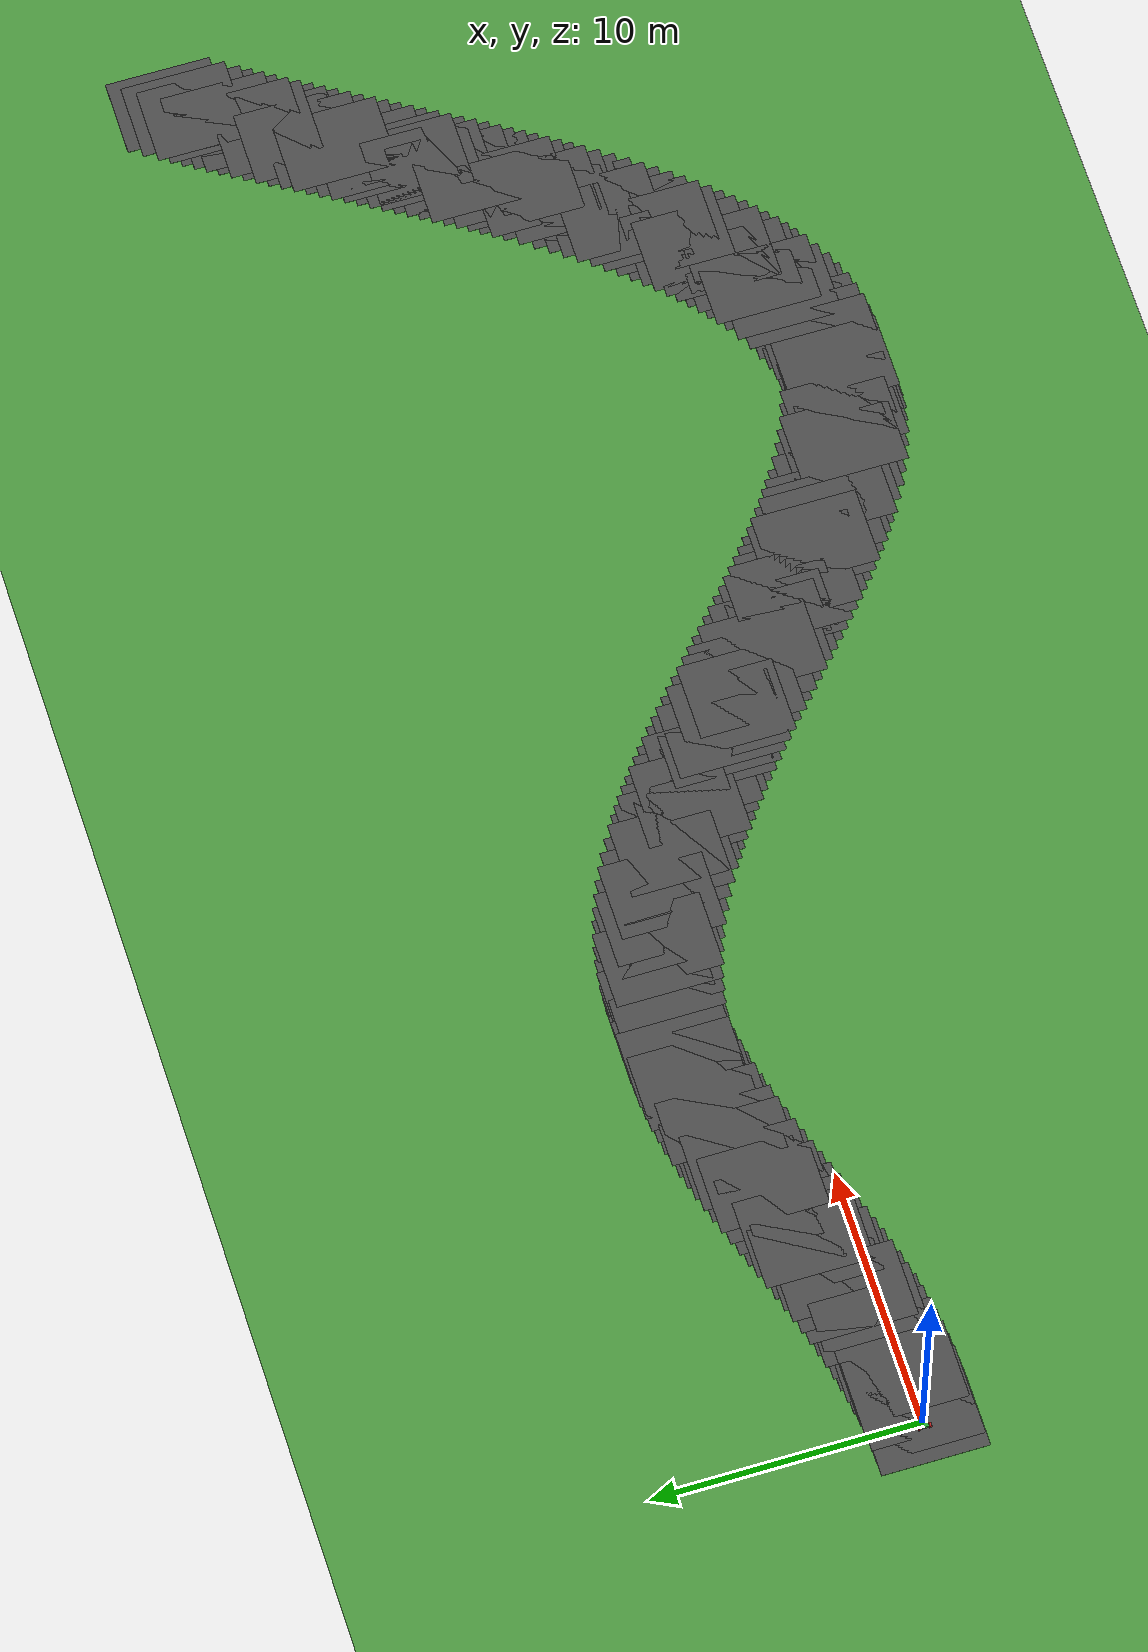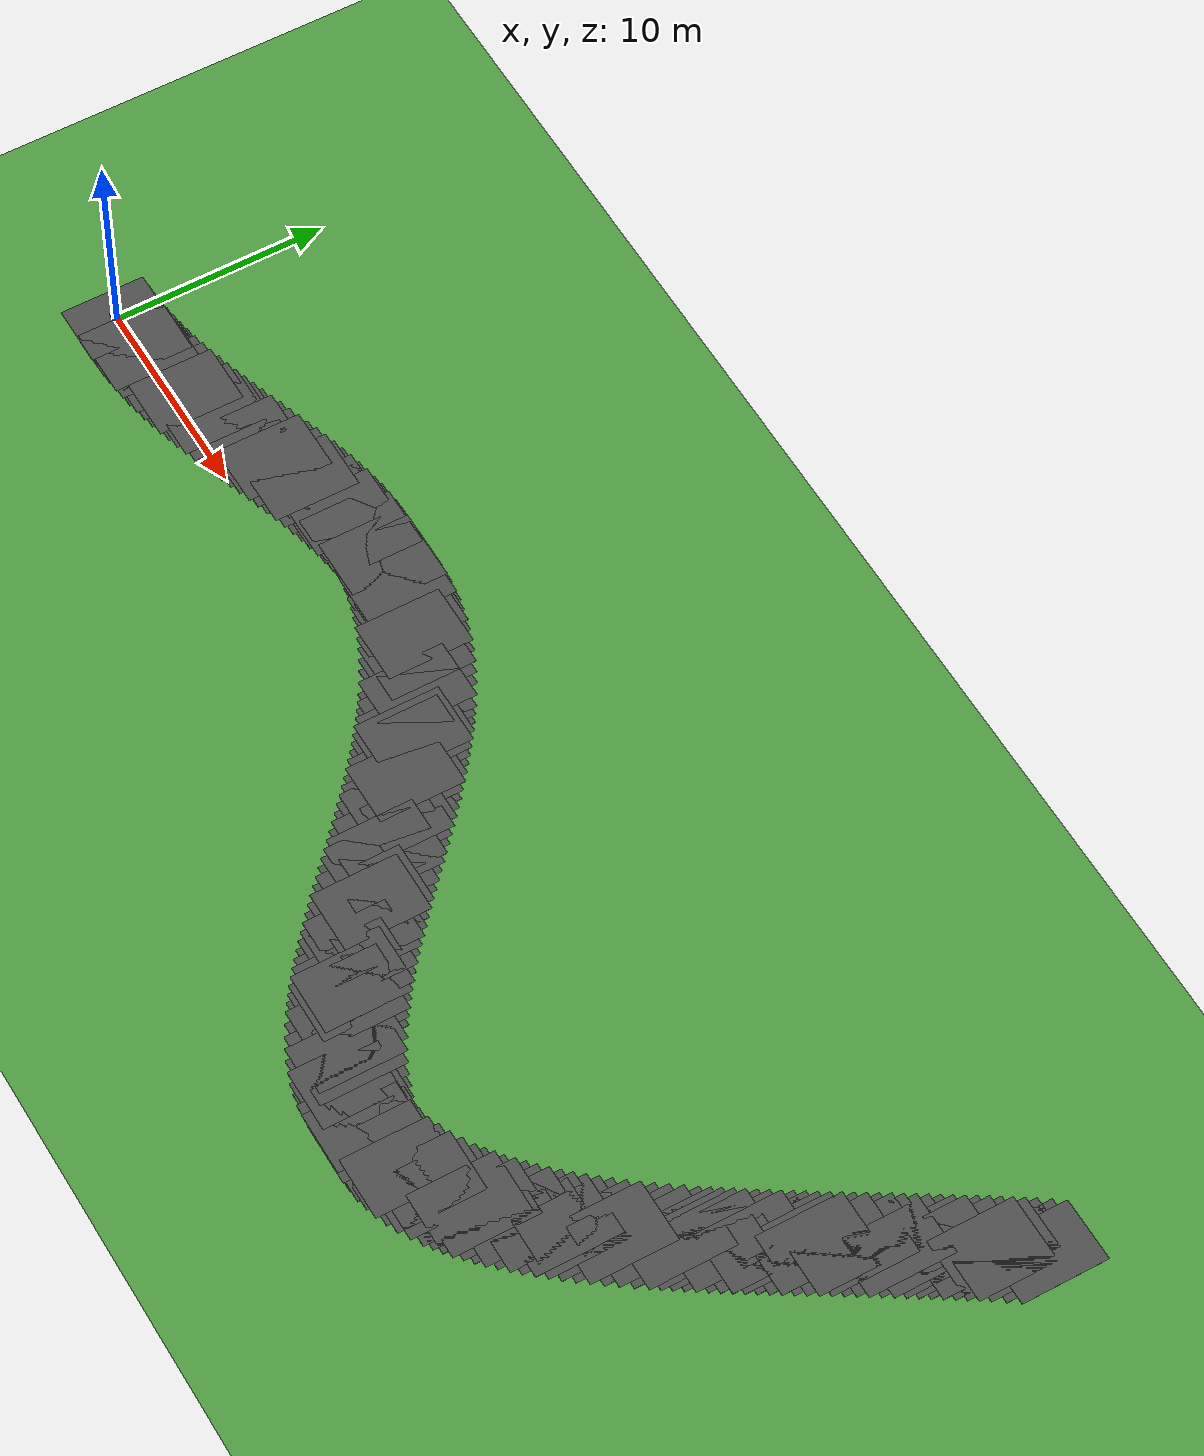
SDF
<sdf version="1.7">
 <world name="default">
  <model name="grass_plane">
   <static>1</static>
   <link name="link">
    <collision name="collision">
     <geometry><plane><normal>0 0 1</normal><size>150 150</size></plane></geometry>
    </collision>
    <visual name="visual">
     <cast_shadows>0</cast_shadows>
     <geometry><plane><normal>0 0 1</normal><size>150 150</size></plane></geometry>
     <material>
      <script><uri>file://media/materials/scripts/gazebo.material</uri><name>Gazebo/Grass</name></script>
     </material>
    </visual>
   </link>
  </model>
  <light name="sun" type="directional">
   <pose>0 0 10 0 -0 0</pose>
   <diffuse>0.8 0.8 0.8 1</diffuse>
   <specular>0.2 0.2 0.2 1</specular>
   <attenuation>
    <range>1000</range>
    <constant>0.9</constant>
    <linear>0.01</linear>
    <quadratic>0.001</quadratic>
   </attenuation>
   <direction>-0.5 0.1 -0.9</direction>
   <spot><inner_angle>0</inner_angle><outer_angle>0</outer_angle><falloff>0</falloff></spot>
  </light>
  <physics name="default_physics" default="0" type="ode">
   <max_step_size>0.001</max_step_size>
   <real_time_factor>1</real_time_factor>
   <real_time_update_rate>1000</real_time_update_rate>
   <gravity>0 0 -9.8066</gravity>
  </physics>
  <gravity>0 0 -9.8</gravity>
  <magnetic_field>6e-06 2.3e-05 -4.2e-05</magnetic_field>
  <atmosphere type="adiabatic"/>
  <scene><ambient>0.4 0.4 0.4 1</ambient><background>0.7 0.7 0.7 1</background><shadows>1</shadows></scene>
  <spherical_coordinates>
   <surface_model>EARTH_WGS84</surface_model>
   <latitude_deg>0</latitude_deg>
   <longitude_deg>0</longitude_deg>
   <elevation>0</elevation>
   <heading_deg>0</heading_deg>
  </spherical_coordinates>
  <model name="steer_bot">
   <link name="base_link">
    <inertial>
     <pose>0.00098 0.00098 0.001961 0 -0 0</pose>
     <mass>5.1</mass>
     <inertia>
      <ixx>0.042913</ixx>
      <ixy>-0.000245098</ixy>
      <ixz>-0.000490196</ixz>
      <iyy>0.10958</iyy>
      <iyz>-0.000490196</iyz>
      <izz>0.142157</izz>
     </inertia>
    </inertial>
    <collision name="base_link_collision"><geometry><box><size>0.5 0.3 0.1</size></box></geometry></collision>
    <collision name="base_link_fixed_joint_lump__imu_box_collision_1">
     <pose>0 0 0.05 0 -0 0</pose>
     <geometry><box><size>0.05 0.05 0.05</size></box></geometry>
    </collision>
    <visual name="base_link_visual">
     <geometry><box><size>0.5 0.3 0.1</size></box></geometry>
     <material>
      <script><name>Gazebo/Green</name><uri>file://media/materials/scripts/gazebo.material</uri></script>
     </material>
    </visual>
    <visual name="base_link_fixed_joint_lump__imu_box_visual_1">
     <pose>0 0 0.05 0 -0 0</pose>
     <geometry><box><size>0.05 0.05 0.05</size></box></geometry>
     <material>
      <script><name>Gazebo/White</name><uri>file://media/materials/scripts/gazebo.material</uri></script>
     </material>
    </visual>
    <sensor name="imu_sensor" type="imu">
     <always_on>1</always_on>
     <update_rate>100</update_rate>
     <visualize>1</visualize>
     <topic>__default_topic__</topic>
     <plugin name="imu_plugin" filename="libgazebo_ros_imu_sensor.so">
      <topicName>imu</topicName>
      <bodyName>imu_link</bodyName>
      <updateRateHZ>10.0</updateRateHZ>
      <gaussianNoise>2.89e-08</gaussianNoise>
      <xyzOffset>0 0 0</xyzOffset>
      <rpyOffset>0 0 0</rpyOffset>
      <frameName>imu_link</frameName>
      <inertialOrientationAsReference>0</inertialOrientationAsReference>
      <robotNamespace>/steer_bot/</robotNamespace>
     </plugin>
     <pose>0 0 0.05 0 -0 0</pose>
    </sensor>
   </link>
   <joint name="front_left_steer_joint" type="revolute">
    <pose relative_to="base_link">0.2 0.2 0.12 0 -0 0</pose>
    <parent>base_link</parent>
    <child>front_left_steer_link</child>
    <axis>
     <xyz>0 0 1</xyz>
     <limit><lower>-0.785398</lower><upper>0.785398</upper><effort>10</effort><velocity>5</velocity></limit>
     <dynamics><spring_reference>0</spring_reference><spring_stiffness>0</spring_stiffness></dynamics>
    </axis>
   </joint>
   <link name="front_left_steer_link">
    <pose relative_to="front_left_steer_joint">0 0 0 0 -0 0</pose>
    <inertial>
     <mass>1</mass>
     <inertia>
      <ixx>0.000658333</ixx>
      <ixy>0</ixy>
      <ixz>0</ixz>
      <iyy>0.000658333</iyy>
      <iyz>0</iyz>
      <izz>0.00125</izz>
     </inertia>
    </inertial>
    <collision name="front_left_steer_link_collision">
     <geometry><cylinder><length>0.02</length><radius>0.05</radius></cylinder></geometry>
    </collision>
    <visual name="front_left_steer_link_visual">
     <geometry><cylinder><length>0.02</length><radius>0.05</radius></cylinder></geometry>
     <material>
      <script><name>Gazebo/Blue</name><uri>file://media/materials/scripts/gazebo.material</uri></script>
     </material>
    </visual>
   </link>
   <joint name="front_left_wheel_joint" type="revolute">
    <pose relative_to="front_left_steer_link">0 0 -0.12 -1.5708 0 0</pose>
    <parent>front_left_steer_link</parent>
    <child>front_left_wheel_link</child>
    <axis>
     <xyz>0 0 1</xyz>
     <limit><lower>-1e+16</lower><upper>1e+16</upper></limit>
     <dynamics><spring_reference>0</spring_reference><spring_stiffness>0</spring_stiffness></dynamics>
    </axis>
   </joint>
   <link name="front_left_wheel_link">
    <pose relative_to="front_left_wheel_joint">0 0 0 0 -0 0</pose>
    <inertial>
     <mass>1</mass>
     <inertia>
      <ixx>0.00303333</ixx>
      <ixy>0</ixy>
      <ixz>0</ixz>
      <iyy>0.00303333</iyy>
      <iyz>0</iyz>
      <izz>0.005</izz>
     </inertia>
    </inertial>
    <collision name="front_left_wheel_link_collision">
     <geometry><cylinder><length>0.08</length><radius>0.1</radius></cylinder></geometry>
    </collision>
    <visual name="front_left_wheel_link_visual">
     <geometry><cylinder><length>0.08</length><radius>0.1</radius></cylinder></geometry>
     <material>
      <script><name>Gazebo/Red</name><uri>file://media/materials/scripts/gazebo.material</uri></script>
     </material>
    </visual>
   </link>
   <joint name="front_right_steer_joint" type="revolute">
    <pose relative_to="base_link">0.2 -0.2 0.12 0 -0 0</pose>
    <parent>base_link</parent>
    <child>front_right_steer_link</child>
    <axis>
     <xyz>0 0 1</xyz>
     <limit><lower>-0.785398</lower><upper>0.785398</upper><effort>10</effort><velocity>5</velocity></limit>
     <dynamics><spring_reference>0</spring_reference><spring_stiffness>0</spring_stiffness></dynamics>
    </axis>
   </joint>
   <link name="front_right_steer_link">
    <pose relative_to="front_right_steer_joint">0 0 0 0 -0 0</pose>
    <inertial>
     <mass>1</mass>
     <inertia>
      <ixx>0.000658333</ixx>
      <ixy>0</ixy>
      <ixz>0</ixz>
      <iyy>0.000658333</iyy>
      <iyz>0</iyz>
      <izz>0.00125</izz>
     </inertia>
    </inertial>
    <collision name="front_right_steer_link_collision">
     <geometry><cylinder><length>0.02</length><radius>0.05</radius></cylinder></geometry>
    </collision>
    <visual name="front_right_steer_link_visual">
     <geometry><cylinder><length>0.02</length><radius>0.05</radius></cylinder></geometry>
     <material>
      <script><name>Gazebo/Blue</name><uri>file://media/materials/scripts/gazebo.material</uri></script>
     </material>
    </visual>
   </link>
   <joint name="front_right_wheel_joint" type="revolute">
    <pose relative_to="front_right_steer_link">0 0 -0.12 -1.5708 0 0</pose>
    <parent>front_right_steer_link</parent>
    <child>front_right_wheel_link</child>
    <axis>
     <xyz>0 0 1</xyz>
     <limit><lower>-1e+16</lower><upper>1e+16</upper></limit>
     <dynamics><spring_reference>0</spring_reference><spring_stiffness>0</spring_stiffness></dynamics>
    </axis>
   </joint>
   <link name="front_right_wheel_link">
    <pose relative_to="front_right_wheel_joint">0 0 0 0 -0 0</pose>
    <inertial>
     <mass>1</mass>
     <inertia>
      <ixx>0.00303333</ixx>
      <ixy>0</ixy>
      <ixz>0</ixz>
      <iyy>0.00303333</iyy>
      <iyz>0</iyz>
      <izz>0.005</izz>
     </inertia>
    </inertial>
    <collision name="front_right_wheel_link_collision">
     <geometry><cylinder><length>0.08</length><radius>0.1</radius></cylinder></geometry>
    </collision>
    <visual name="front_right_wheel_link_visual">
     <geometry><cylinder><length>0.08</length><radius>0.1</radius></cylinder></geometry>
     <material>
      <script><name>Gazebo/Red</name><uri>file://media/materials/scripts/gazebo.material</uri></script>
     </material>
    </visual>
   </link>
   <joint name="front_steer_joint" type="revolute">
    <pose relative_to="base_link">0.2 0 0.12 0 -0 0</pose>
    <parent>base_link</parent>
    <child>front_steer_link</child>
    <axis>
     <xyz>0 0 1</xyz>
     <limit><lower>-3.14159</lower><upper>3.14159</upper><effort>10</effort><velocity>5</velocity></limit>
     <dynamics><spring_reference>0</spring_reference><spring_stiffness>0</spring_stiffness></dynamics>
    </axis>
   </joint>
   <link name="front_steer_link">
    <pose relative_to="front_steer_joint">0 0 0 0 -0 0</pose>
    <inertial>
     <mass>1</mass>
     <inertia>
      <ixx>0.000658333</ixx>
      <ixy>0</ixy>
      <ixz>0</ixz>
      <iyy>0.000658333</iyy>
      <iyz>0</iyz>
      <izz>0.00125</izz>
     </inertia>
    </inertial>
    <collision name="front_steer_link_collision">
     <geometry><cylinder><length>0.02</length><radius>0.05</radius></cylinder></geometry>
    </collision>
    <visual name="front_steer_link_visual">
     <geometry><cylinder><length>0.02</length><radius>0.05</radius></cylinder></geometry>
     <material>
      <script><name>Gazebo/Yellow</name><uri>file://media/materials/scripts/gazebo.material</uri></script>
     </material>
    </visual>
   </link>
   <joint name="rear_left_wheel_joint" type="revolute">
    <pose relative_to="base_link">-0.2 0.2 0 -1.5708 0 0</pose>
    <parent>base_link</parent>
    <child>rear_left_wheel_link</child>
    <axis>
     <xyz>0 0 1</xyz>
     <limit><lower>-1e+16</lower><upper>1e+16</upper></limit>
     <dynamics><spring_reference>0</spring_reference><spring_stiffness>0</spring_stiffness></dynamics>
    </axis>
   </joint>
   <link name="rear_left_wheel_link">
    <pose relative_to="rear_left_wheel_joint">0 0 0 0 -0 0</pose>
    <inertial>
     <mass>1</mass>
     <inertia>
      <ixx>0.00303333</ixx>
      <ixy>0</ixy>
      <ixz>0</ixz>
      <iyy>0.00303333</iyy>
      <iyz>0</iyz>
      <izz>0.005</izz>
     </inertia>
    </inertial>
    <collision name="rear_left_wheel_link_collision">
     <geometry><cylinder><length>0.08</length><radius>0.1</radius></cylinder></geometry>
    </collision>
    <visual name="rear_left_wheel_link_visual">
     <geometry><cylinder><length>0.08</length><radius>0.1</radius></cylinder></geometry>
     <material>
      <script><name>Gazebo/Red</name><uri>file://media/materials/scripts/gazebo.material</uri></script>
     </material>
    </visual>
   </link>
   <joint name="rear_right_wheel_joint" type="revolute">
    <pose relative_to="base_link">-0.2 -0.2 0 -1.5708 0 0</pose>
    <parent>base_link</parent>
    <child>rear_right_wheel_link</child>
    <axis>
     <xyz>0 0 1</xyz>
     <limit><lower>-1e+16</lower><upper>1e+16</upper></limit>
     <dynamics><spring_reference>0</spring_reference><spring_stiffness>0</spring_stiffness></dynamics>
    </axis>
   </joint>
   <link name="rear_right_wheel_link">
    <pose relative_to="rear_right_wheel_joint">0 0 0 0 -0 0</pose>
    <inertial>
     <mass>1</mass>
     <inertia>
      <ixx>0.00303333</ixx>
      <ixy>0</ixy>
      <ixz>0</ixz>
      <iyy>0.00303333</iyy>
      <iyz>0</iyz>
      <izz>0.005</izz>
     </inertia>
    </inertial>
    <collision name="rear_right_wheel_link_collision">
     <geometry><cylinder><length>0.08</length><radius>0.1</radius></cylinder></geometry>
    </collision>
    <visual name="rear_right_wheel_link_visual">
     <geometry><cylinder><length>0.08</length><radius>0.1</radius></cylinder></geometry>
     <material>
      <script><name>Gazebo/Red</name><uri>file://media/materials/scripts/gazebo.material</uri></script>
     </material>
    </visual>
   </link>
   <joint name="rear_wheel_joint" type="revolute">
    <pose relative_to="base_link">-0.2 0 0 -1.5708 0 0</pose>
    <parent>base_link</parent>
    <child>rear_wheel_link</child>
    <axis>
     <xyz>0 0 1</xyz>
     <limit><lower>-1e+16</lower><upper>1e+16</upper></limit>
     <dynamics><spring_reference>0</spring_reference><spring_stiffness>0</spring_stiffness></dynamics>
    </axis>
   </joint>
   <link name="rear_wheel_link">
    <pose relative_to="rear_wheel_joint">0 0 0 0 -0 0</pose>
    <inertial>
     <mass>0.03125</mass>
     <inertia>
      <ixx>9.04948e-06</ixx>
      <ixy>0</ixy>
      <ixz>0</ixz>
      <iyy>9.04948e-06</iyy>
      <iyz>0</iyz>
      <izz>9.76563e-06</izz>
     </inertia>
    </inertial>
    <collision name="rear_wheel_link_collision">
     <geometry><cylinder><length>0.04</length><radius>0.025</radius></cylinder></geometry>
    </collision>
    <visual name="rear_wheel_link_visual">
     <geometry><cylinder><length>0.04</length><radius>0.025</radius></cylinder></geometry>
     <material>
      <script><name>Gazebo/Yellow</name><uri>file://media/materials/scripts/gazebo.material</uri></script>
     </material>
    </visual>
   </link>
   <static>0</static>
   <plugin name="gazebo_ros_control" filename="libgazebo_ros_control.so">
    <robotNamespace>/steer_bot</robotNamespace>
    <robotSimType>steer_bot_hardware_gazebo/SteerBotHardwareGazebo</robotSimType>
    <legacyModeNS>0</legacyModeNS>
   </plugin>
   <plugin name="p3d_base_controller" filename="libgazebo_ros_p3d.so">
    <alwaysOn>1</alwaysOn>
    <updateRate>50.0</updateRate>
    <bodyName>base_link</bodyName>
    <topicName>pose_ground_truth</topicName>
    <gaussianNoise>0.00</gaussianNoise>
    <frameName>world</frameName>
    <xyzOffsets>0 0 0</xyzOffsets>
    <rpyOffsets>0 0 0</rpyOffsets>
    <robotNamespace>/steer_bot/</robotNamespace>
   </plugin>
   <pose>-0.000916 0.000112 0.105 1e-06 -1e-06 -8.4e-05</pose>
  </model>
  <model name="roadSegment_0_0">
   <static>1</static>
   <link name="link">
    <collision name="collision"><geometry><box><size>3 4 0.01</size></box></geometry></collision>
    <visual name="visual">
     <cast_shadows>0</cast_shadows>
     <geometry><box><size>3 4 0.01</size></box></geometry>
     <material>
      <script>
       <uri>model://asphalt_plane/materials/scripts</uri>
       <uri>model://asphalt_plane/materials/textures</uri>
       <name>vrc/asphalt</name>
      </script>
     </material>
    </visual>
   </link>
  </model>
  <model name="roadSegment_0_1">
   <static>1</static>
   <link name="link">
    <collision name="collision"><geometry><box><size>3 4 0.01</size></box></geometry></collision>
    <visual name="visual">
     <cast_shadows>0</cast_shadows>
     <geometry><box><size>3 4 0.01</size></box></geometry>
     <material>
      <script>
       <uri>model://asphalt_plane/materials/scripts</uri>
       <uri>model://asphalt_plane/materials/textures</uri>
       <name>vrc/asphalt</name>
      </script>
     </material>
    </visual>
   </link>
   <pose>0.5 0.01497 0 0 -0 0</pose>
  </model>
  <model name="roadSegment_1_0">
   <static>1</static>
   <link name="link">
    <collision name="collision"><geometry><box><size>3 4 0.01</size></box></geometry></collision>
    <visual name="visual">
     <cast_shadows>0</cast_shadows>
     <geometry><box><size>3 4 0.01</size></box></geometry>
     <material>
      <script>
       <uri>model://asphalt_plane/materials/scripts</uri>
       <uri>model://asphalt_plane/materials/textures</uri>
       <name>vrc/asphalt</name>
      </script>
     </material>
    </visual>
   </link>
   <pose>1 0.02994 0 0 -0 0</pose>
  </model>
  <model name="roadSegment_1_1">
   <static>1</static>
   <link name="link">
    <collision name="collision"><geometry><box><size>3 4 0.01</size></box></geometry></collision>
    <visual name="visual">
     <cast_shadows>0</cast_shadows>
     <geometry><box><size>3 4 0.01</size></box></geometry>
     <material>
      <script>
       <uri>model://asphalt_plane/materials/scripts</uri>
       <uri>model://asphalt_plane/materials/textures</uri>
       <name>vrc/asphalt</name>
      </script>
     </material>
    </visual>
   </link>
   <pose>1.5 0.074419 0 0 -0 0</pose>
  </model>
  <model name="roadSegment_2_0">
   <static>1</static>
   <link name="link">
    <collision name="collision"><geometry><box><size>3 4 0.01</size></box></geometry></collision>
    <visual name="visual">
     <cast_shadows>0</cast_shadows>
     <geometry><box><size>3 4 0.01</size></box></geometry>
     <material>
      <script>
       <uri>model://asphalt_plane/materials/scripts</uri>
       <uri>model://asphalt_plane/materials/textures</uri>
       <name>vrc/asphalt</name>
      </script>
     </material>
    </visual>
   </link>
   <pose>2 0.118898 0 0 -0 0</pose>
  </model>
  <model name="roadSegment_2_1">
   <static>1</static>
   <link name="link">
    <collision name="collision"><geometry><box><size>3 4 0.01</size></box></geometry></collision>
    <visual name="visual">
     <cast_shadows>0</cast_shadows>
     <geometry><box><size>3 4 0.01</size></box></geometry>
     <material>
      <script>
       <uri>model://asphalt_plane/materials/scripts</uri>
       <uri>model://asphalt_plane/materials/textures</uri>
       <name>vrc/asphalt</name>
      </script>
     </material>
    </visual>
   </link>
   <pose>2.5 0.191602 0 0 -0 0</pose>
  </model>
  <model name="roadSegment_3_0">
   <static>1</static>
   <link name="link">
    <collision name="collision"><geometry><box><size>3 4 0.01</size></box></geometry></collision>
    <visual name="visual">
     <cast_shadows>0</cast_shadows>
     <geometry><box><size>3 4 0.01</size></box></geometry>
     <material>
      <script>
       <uri>model://asphalt_plane/materials/scripts</uri>
       <uri>model://asphalt_plane/materials/textures</uri>
       <name>vrc/asphalt</name>
      </script>
     </material>
    </visual>
   </link>
   <pose>3 0.264307 0 0 -0 0</pose>
  </model>
  <model name="roadSegment_3_1">
   <static>1</static>
   <link name="link">
    <collision name="collision"><geometry><box><size>3 4 0.01</size></box></geometry></collision>
    <visual name="visual">
     <cast_shadows>0</cast_shadows>
     <geometry><box><size>3 4 0.01</size></box></geometry>
     <material>
      <script>
       <uri>model://asphalt_plane/materials/scripts</uri>
       <uri>model://asphalt_plane/materials/textures</uri>
       <name>vrc/asphalt</name>
      </script>
     </material>
    </visual>
   </link>
   <pose>3.5 0.363128 0 0 -0 0</pose>
  </model>
  <model name="roadSegment_4_0">
   <static>1</static>
   <link name="link">
    <collision name="collision"><geometry><box><size>3 4 0.01</size></box></geometry></collision>
    <visual name="visual">
     <cast_shadows>0</cast_shadows>
     <geometry><box><size>3 4 0.01</size></box></geometry>
     <material>
      <script>
       <uri>model://asphalt_plane/materials/scripts</uri>
       <uri>model://asphalt_plane/materials/textures</uri>
       <name>vrc/asphalt</name>
      </script>
     </material>
    </visual>
   </link>
   <pose>4 0.46195 0 0 -0 0</pose>
  </model>
  <model name="roadSegment_4_1">
   <static>1</static>
   <link name="link">
    <collision name="collision"><geometry><box><size>3 4 0.01</size></box></geometry></collision>
    <visual name="visual">
     <cast_shadows>0</cast_shadows>
     <geometry><box><size>3 4 0.01</size></box></geometry>
     <material>
      <script>
       <uri>model://asphalt_plane/materials/scripts</uri>
       <uri>model://asphalt_plane/materials/textures</uri>
       <name>vrc/asphalt</name>
      </script>
     </material>
    </visual>
   </link>
   <pose>4.5 0.584 0 0 -0 0</pose>
  </model>
  <model name="roadSegment_5_0">
   <static>1</static>
   <link name="link">
    <collision name="collision"><geometry><box><size>3 4 0.01</size></box></geometry></collision>
    <visual name="visual">
     <cast_shadows>0</cast_shadows>
     <geometry><box><size>3 4 0.01</size></box></geometry>
     <material>
      <script>
       <uri>model://asphalt_plane/materials/scripts</uri>
       <uri>model://asphalt_plane/materials/textures</uri>
       <name>vrc/asphalt</name>
      </script>
     </material>
    </visual>
   </link>
   <pose>5 0.706051 0 0 -0 0</pose>
  </model>
  <model name="roadSegment_5_1">
   <static>1</static>
   <link name="link">
    <collision name="collision"><geometry><box><size>3 4 0.01</size></box></geometry></collision>
    <visual name="visual">
     <cast_shadows>0</cast_shadows>
     <geometry><box><size>3 4 0.01</size></box></geometry>
     <material>
      <script>
       <uri>model://asphalt_plane/materials/scripts</uri>
       <uri>model://asphalt_plane/materials/textures</uri>
       <name>vrc/asphalt</name>
      </script>
     </material>
    </visual>
   </link>
   <pose>5.5 0.847726 0 0 -0 0</pose>
  </model>
  <model name="roadSegment_6_0">
   <static>1</static>
   <link name="link">
    <collision name="collision"><geometry><box><size>3 4 0.01</size></box></geometry></collision>
    <visual name="visual">
     <cast_shadows>0</cast_shadows>
     <geometry><box><size>3 4 0.01</size></box></geometry>
     <material>
      <script>
       <uri>model://asphalt_plane/materials/scripts</uri>
       <uri>model://asphalt_plane/materials/textures</uri>
       <name>vrc/asphalt</name>
      </script>
     </material>
    </visual>
   </link>
   <pose>6 0.989402 0 0 -0 0</pose>
  </model>
  <model name="roadSegment_6_1">
   <static>1</static>
   <link name="link">
    <collision name="collision"><geometry><box><size>3 4 0.01</size></box></geometry></collision>
    <visual name="visual">
     <cast_shadows>0</cast_shadows>
     <geometry><box><size>3 4 0.01</size></box></geometry>
     <material>
      <script>
       <uri>model://asphalt_plane/materials/scripts</uri>
       <uri>model://asphalt_plane/materials/textures</uri>
       <name>vrc/asphalt</name>
      </script>
     </material>
    </visual>
   </link>
   <pose>6.5 1.14646 0 0 -0 0</pose>
  </model>
  <model name="roadSegment_7_0">
   <static>1</static>
   <link name="link">
    <collision name="collision"><geometry><box><size>3 4 0.01</size></box></geometry></collision>
    <visual name="visual">
     <cast_shadows>0</cast_shadows>
     <geometry><box><size>3 4 0.01</size></box></geometry>
     <material>
      <script>
       <uri>model://asphalt_plane/materials/scripts</uri>
       <uri>model://asphalt_plane/materials/textures</uri>
       <name>vrc/asphalt</name>
      </script>
     </material>
    </visual>
   </link>
   <pose>7 1.30352 0 0 -0 0</pose>
  </model>
  <model name="roadSegment_7_1">
   <static>1</static>
   <link name="link">
    <collision name="collision"><geometry><box><size>3 4 0.01</size></box></geometry></collision>
    <visual name="visual">
     <cast_shadows>0</cast_shadows>
     <geometry><box><size>3 4 0.01</size></box></geometry>
     <material>
      <script>
       <uri>model://asphalt_plane/materials/scripts</uri>
       <uri>model://asphalt_plane/materials/textures</uri>
       <name>vrc/asphalt</name>
      </script>
     </material>
    </visual>
   </link>
   <pose>7.5 1.47117 0 0 -0 0</pose>
  </model>
  <model name="roadSegment_8_0">
   <static>1</static>
   <link name="link">
    <collision name="collision"><geometry><box><size>3 4 0.01</size></box></geometry></collision>
    <visual name="visual">
     <cast_shadows>0</cast_shadows>
     <geometry><box><size>3 4 0.01</size></box></geometry>
     <material>
      <script>
       <uri>model://asphalt_plane/materials/scripts</uri>
       <uri>model://asphalt_plane/materials/textures</uri>
       <name>vrc/asphalt</name>
      </script>
     </material>
    </visual>
   </link>
   <pose>8 1.63882 0 0 -0 0</pose>
  </model>
  <model name="roadSegment_8_1">
   <static>1</static>
   <link name="link">
    <collision name="collision"><geometry><box><size>3 4 0.01</size></box></geometry></collision>
    <visual name="visual">
     <cast_shadows>0</cast_shadows>
     <geometry><box><size>3 4 0.01</size></box></geometry>
     <material>
      <script>
       <uri>model://asphalt_plane/materials/scripts</uri>
       <uri>model://asphalt_plane/materials/textures</uri>
       <name>vrc/asphalt</name>
      </script>
     </material>
    </visual>
   </link>
   <pose>8.5 1.81184 0 0 -0 0</pose>
  </model>
  <model name="roadSegment_9_0">
   <static>1</static>
   <link name="link">
    <collision name="collision"><geometry><box><size>3 4 0.01</size></box></geometry></collision>
    <visual name="visual">
     <cast_shadows>0</cast_shadows>
     <geometry><box><size>3 4 0.01</size></box></geometry>
     <material>
      <script>
       <uri>model://asphalt_plane/materials/scripts</uri>
       <uri>model://asphalt_plane/materials/textures</uri>
       <name>vrc/asphalt</name>
      </script>
     </material>
    </visual>
   </link>
   <pose>9 1.98486 0 0 -0 0</pose>
  </model>
  <model name="roadSegment_9_1">
   <static>1</static>
   <link name="link">
    <collision name="collision"><geometry><box><size>3 4 0.01</size></box></geometry></collision>
    <visual name="visual">
     <cast_shadows>0</cast_shadows>
     <geometry><box><size>3 4 0.01</size></box></geometry>
     <material>
      <script>
       <uri>model://asphalt_plane/materials/scripts</uri>
       <uri>model://asphalt_plane/materials/textures</uri>
       <name>vrc/asphalt</name>
      </script>
     </material>
    </visual>
   </link>
   <pose>9.5 2.1577 0 0 -0 0</pose>
  </model>
  <model name="roadSegment_10_0">
   <static>1</static>
   <link name="link">
    <collision name="collision"><geometry><box><size>3 4 0.01</size></box></geometry></collision>
    <visual name="visual">
     <cast_shadows>0</cast_shadows>
     <geometry><box><size>3 4 0.01</size></box></geometry>
     <material>
      <script>
       <uri>model://asphalt_plane/materials/scripts</uri>
       <uri>model://asphalt_plane/materials/textures</uri>
       <name>vrc/asphalt</name>
      </script>
     </material>
    </visual>
   </link>
   <pose>10 2.33053 0 0 -0 0</pose>
  </model>
  <model name="roadSegment_10_1">
   <static>1</static>
   <link name="link">
    <collision name="collision"><geometry><box><size>3 4 0.01</size></box></geometry></collision>
    <visual name="visual">
     <cast_shadows>0</cast_shadows>
     <geometry><box><size>3 4 0.01</size></box></geometry>
     <material>
      <script>
       <uri>model://asphalt_plane/materials/scripts</uri>
       <uri>model://asphalt_plane/materials/textures</uri>
       <name>vrc/asphalt</name>
      </script>
     </material>
    </visual>
   </link>
   <pose>10.5 2.49743 0 0 -0 0</pose>
  </model>
  <model name="roadSegment_11_0">
   <static>1</static>
   <link name="link">
    <collision name="collision"><geometry><box><size>3 4 0.01</size></box></geometry></collision>
    <visual name="visual">
     <cast_shadows>0</cast_shadows>
     <geometry><box><size>3 4 0.01</size></box></geometry>
     <material>
      <script>
       <uri>model://asphalt_plane/materials/scripts</uri>
       <uri>model://asphalt_plane/materials/textures</uri>
       <name>vrc/asphalt</name>
      </script>
     </material>
    </visual>
   </link>
   <pose>11 2.66433 0 0 -0 0</pose>
  </model>
  <model name="roadSegment_11_1">
   <static>1</static>
   <link name="link">
    <collision name="collision"><geometry><box><size>3 4 0.01</size></box></geometry></collision>
    <visual name="visual">
     <cast_shadows>0</cast_shadows>
     <geometry><box><size>3 4 0.01</size></box></geometry>
     <material>
      <script>
       <uri>model://asphalt_plane/materials/scripts</uri>
       <uri>model://asphalt_plane/materials/textures</uri>
       <name>vrc/asphalt</name>
      </script>
     </material>
    </visual>
   </link>
   <pose>11.5 2.81946 0 0 -0 0</pose>
  </model>
  <model name="roadSegment_12_0">
   <static>1</static>
   <link name="link">
    <collision name="collision"><geometry><box><size>3 4 0.01</size></box></geometry></collision>
    <visual name="visual">
     <cast_shadows>0</cast_shadows>
     <geometry><box><size>3 4 0.01</size></box></geometry>
     <material>
      <script>
       <uri>model://asphalt_plane/materials/scripts</uri>
       <uri>model://asphalt_plane/materials/textures</uri>
       <name>vrc/asphalt</name>
      </script>
     </material>
    </visual>
   </link>
   <pose>12 2.9746 0 0 -0 0</pose>
  </model>
  <model name="roadSegment_12_1">
   <static>1</static>
   <link name="link">
    <collision name="collision"><geometry><box><size>3 4 0.01</size></box></geometry></collision>
    <visual name="visual">
     <cast_shadows>0</cast_shadows>
     <geometry><box><size>3 4 0.01</size></box></geometry>
     <material>
      <script>
       <uri>model://asphalt_plane/materials/scripts</uri>
       <uri>model://asphalt_plane/materials/textures</uri>
       <name>vrc/asphalt</name>
      </script>
     </material>
    </visual>
   </link>
   <pose>12.5 3.11222 0 0 -0 0</pose>
  </model>
  <model name="roadSegment_13_0">
   <static>1</static>
   <link name="link">
    <collision name="collision"><geometry><box><size>3 4 0.01</size></box></geometry></collision>
    <visual name="visual">
     <cast_shadows>0</cast_shadows>
     <geometry><box><size>3 4 0.01</size></box></geometry>
     <material>
      <script>
       <uri>model://asphalt_plane/materials/scripts</uri>
       <uri>model://asphalt_plane/materials/textures</uri>
       <name>vrc/asphalt</name>
      </script>
     </material>
    </visual>
   </link>
   <pose>13 3.24983 0 0 -0 0</pose>
  </model>
  <model name="roadSegment_13_1">
   <static>1</static>
   <link name="link">
    <collision name="collision"><geometry><box><size>3 4 0.01</size></box></geometry></collision>
    <visual name="visual">
     <cast_shadows>0</cast_shadows>
     <geometry><box><size>3 4 0.01</size></box></geometry>
     <material>
      <script>
       <uri>model://asphalt_plane/materials/scripts</uri>
       <uri>model://asphalt_plane/materials/textures</uri>
       <name>vrc/asphalt</name>
      </script>
     </material>
    </visual>
   </link>
   <pose>13.5 3.36436 0 0 -0 0</pose>
  </model>
  <model name="roadSegment_14_0">
   <static>1</static>
   <link name="link">
    <collision name="collision"><geometry><box><size>3 4 0.01</size></box></geometry></collision>
    <visual name="visual">
     <cast_shadows>0</cast_shadows>
     <geometry><box><size>3 4 0.01</size></box></geometry>
     <material>
      <script>
       <uri>model://asphalt_plane/materials/scripts</uri>
       <uri>model://asphalt_plane/materials/textures</uri>
       <name>vrc/asphalt</name>
      </script>
     </material>
    </visual>
   </link>
   <pose>14 3.47889 0 0 -0 0</pose>
  </model>
  <model name="roadSegment_14_1">
   <static>1</static>
   <link name="link">
    <collision name="collision"><geometry><box><size>3 4 0.01</size></box></geometry></collision>
    <visual name="visual">
     <cast_shadows>0</cast_shadows>
     <geometry><box><size>3 4 0.01</size></box></geometry>
     <material>
      <script>
       <uri>model://asphalt_plane/materials/scripts</uri>
       <uri>model://asphalt_plane/materials/textures</uri>
       <name>vrc/asphalt</name>
      </script>
     </material>
    </visual>
   </link>
   <pose>14.5 3.5651 0 0 -0 0</pose>
  </model>
  <model name="roadSegment_15_0">
   <static>1</static>
   <link name="link">
    <collision name="collision"><geometry><box><size>3 4 0.01</size></box></geometry></collision>
    <visual name="visual">
     <cast_shadows>0</cast_shadows>
     <geometry><box><size>3 4 0.01</size></box></geometry>
     <material>
      <script>
       <uri>model://asphalt_plane/materials/scripts</uri>
       <uri>model://asphalt_plane/materials/textures</uri>
       <name>vrc/asphalt</name>
      </script>
     </material>
    </visual>
   </link>
   <pose>15 3.65131 0 0 -0 0</pose>
  </model>
  <model name="roadSegment_15_1">
   <static>1</static>
   <link name="link">
    <collision name="collision"><geometry><box><size>3 4 0.01</size></box></geometry></collision>
    <visual name="visual">
     <cast_shadows>0</cast_shadows>
     <geometry><box><size>3 4 0.01</size></box></geometry>
     <material>
      <script>
       <uri>model://asphalt_plane/materials/scripts</uri>
       <uri>model://asphalt_plane/materials/textures</uri>
       <name>vrc/asphalt</name>
      </script>
     </material>
    </visual>
   </link>
   <pose>15.5 3.70442 0 0 -0 0</pose>
  </model>
  <model name="roadSegment_16_0">
   <static>1</static>
   <link name="link">
    <collision name="collision"><geometry><box><size>3 4 0.01</size></box></geometry></collision>
    <visual name="visual">
     <cast_shadows>0</cast_shadows>
     <geometry><box><size>3 4 0.01</size></box></geometry>
     <material>
      <script>
       <uri>model://asphalt_plane/materials/scripts</uri>
       <uri>model://asphalt_plane/materials/textures</uri>
       <name>vrc/asphalt</name>
      </script>
     </material>
    </visual>
   </link>
   <pose>16 3.75753 0 0 -0 0</pose>
  </model>
  <model name="roadSegment_16_1">
   <static>1</static>
   <link name="link">
    <collision name="collision"><geometry><box><size>3 4 0.01</size></box></geometry></collision>
    <visual name="visual">
     <cast_shadows>0</cast_shadows>
     <geometry><box><size>3 4 0.01</size></box></geometry>
     <material>
      <script>
       <uri>model://asphalt_plane/materials/scripts</uri>
       <uri>model://asphalt_plane/materials/textures</uri>
       <name>vrc/asphalt</name>
      </script>
     </material>
    </visual>
   </link>
   <pose>16.5 3.77333 0 0 -0 0</pose>
  </model>
  <model name="roadSegment_17_0">
   <static>1</static>
   <link name="link">
    <collision name="collision"><geometry><box><size>3 4 0.01</size></box></geometry></collision>
    <visual name="visual">
     <cast_shadows>0</cast_shadows>
     <geometry><box><size>3 4 0.01</size></box></geometry>
     <material>
      <script>
       <uri>model://asphalt_plane/materials/scripts</uri>
       <uri>model://asphalt_plane/materials/textures</uri>
       <name>vrc/asphalt</name>
      </script>
     </material>
    </visual>
   </link>
   <pose>17 3.78913 0 0 -0 0</pose>
  </model>
  <model name="roadSegment_17_1">
   <static>1</static>
   <link name="link">
    <collision name="collision"><geometry><box><size>3 4 0.01</size></box></geometry></collision>
    <visual name="visual">
     <cast_shadows>0</cast_shadows>
     <geometry><box><size>3 4 0.01</size></box></geometry>
     <material>
      <script>
       <uri>model://asphalt_plane/materials/scripts</uri>
       <uri>model://asphalt_plane/materials/textures</uri>
       <name>vrc/asphalt</name>
      </script>
     </material>
    </visual>
   </link>
   <pose>17.5 3.76409 0 0 -0 0</pose>
  </model>
  <model name="roadSegment_18_0">
   <static>1</static>
   <link name="link">
    <collision name="collision"><geometry><box><size>3 4 0.01</size></box></geometry></collision>
    <visual name="visual">
     <cast_shadows>0</cast_shadows>
     <geometry><box><size>3 4 0.01</size></box></geometry>
     <material>
      <script>
       <uri>model://asphalt_plane/materials/scripts</uri>
       <uri>model://asphalt_plane/materials/textures</uri>
       <name>vrc/asphalt</name>
      </script>
     </material>
    </visual>
   </link>
   <pose>18 3.73906 0 0 -0 0</pose>
  </model>
  <model name="roadSegment_18_1">
   <static>1</static>
   <link name="link">
    <collision name="collision"><geometry><box><size>3 4 0.01</size></box></geometry></collision>
    <visual name="visual">
     <cast_shadows>0</cast_shadows>
     <geometry><box><size>3 4 0.01</size></box></geometry>
     <material>
      <script>
       <uri>model://asphalt_plane/materials/scripts</uri>
       <uri>model://asphalt_plane/materials/textures</uri>
       <name>vrc/asphalt</name>
      </script>
     </material>
    </visual>
   </link>
   <pose>18.5 3.67046 0 0 -0 0</pose>
  </model>
  <model name="roadSegment_19_0">
   <static>1</static>
   <link name="link">
    <collision name="collision"><geometry><box><size>3 4 0.01</size></box></geometry></collision>
    <visual name="visual">
     <cast_shadows>0</cast_shadows>
     <geometry><box><size>3 4 0.01</size></box></geometry>
     <material>
      <script>
       <uri>model://asphalt_plane/materials/scripts</uri>
       <uri>model://asphalt_plane/materials/textures</uri>
       <name>vrc/asphalt</name>
      </script>
     </material>
    </visual>
   </link>
   <pose>19 3.60186 0 0 -0 0</pose>
  </model>
  <model name="roadSegment_19_1">
   <static>1</static>
   <link name="link">
    <collision name="collision"><geometry><box><size>3 4 0.01</size></box></geometry></collision>
    <visual name="visual">
     <cast_shadows>0</cast_shadows>
     <geometry><box><size>3 4 0.01</size></box></geometry>
     <material>
      <script>
       <uri>model://asphalt_plane/materials/scripts</uri>
       <uri>model://asphalt_plane/materials/textures</uri>
       <name>vrc/asphalt</name>
      </script>
     </material>
    </visual>
   </link>
   <pose>19.5 3.48782 0 0 -0 0</pose>
  </model>
  <model name="roadSegment_20_0">
   <static>1</static>
   <link name="link">
    <collision name="collision"><geometry><box><size>3 4 0.01</size></box></geometry></collision>
    <visual name="visual">
     <cast_shadows>0</cast_shadows>
     <geometry><box><size>3 4 0.01</size></box></geometry>
     <material>
      <script>
       <uri>model://asphalt_plane/materials/scripts</uri>
       <uri>model://asphalt_plane/materials/textures</uri>
       <name>vrc/asphalt</name>
      </script>
     </material>
    </visual>
   </link>
   <pose>20 3.37377 0 0 -0 0</pose>
  </model>
  <model name="roadSegment_20_1">
   <static>1</static>
   <link name="link">
    <collision name="collision"><geometry><box><size>3 4 0.01</size></box></geometry></collision>
    <visual name="visual">
     <cast_shadows>0</cast_shadows>
     <geometry><box><size>3 4 0.01</size></box></geometry>
     <material>
      <script>
       <uri>model://asphalt_plane/materials/scripts</uri>
       <uri>model://asphalt_plane/materials/textures</uri>
       <name>vrc/asphalt</name>
      </script>
     </material>
    </visual>
   </link>
   <pose>20.5 3.21335 0 0 -0 0</pose>
  </model>
  <model name="roadSegment_21_0">
   <static>1</static>
   <link name="link">
    <collision name="collision"><geometry><box><size>3 4 0.01</size></box></geometry></collision>
    <visual name="visual">
     <cast_shadows>0</cast_shadows>
     <geometry><box><size>3 4 0.01</size></box></geometry>
     <material>
      <script>
       <uri>model://asphalt_plane/materials/scripts</uri>
       <uri>model://asphalt_plane/materials/textures</uri>
       <name>vrc/asphalt</name>
      </script>
     </material>
    </visual>
   </link>
   <pose>21 3.05293 0 0 -0 0</pose>
  </model>
  <model name="roadSegment_21_1">
   <static>1</static>
   <link name="link">
    <collision name="collision"><geometry><box><size>3 4 0.01</size></box></geometry></collision>
    <visual name="visual">
     <cast_shadows>0</cast_shadows>
     <geometry><box><size>3 4 0.01</size></box></geometry>
     <material>
      <script>
       <uri>model://asphalt_plane/materials/scripts</uri>
       <uri>model://asphalt_plane/materials/textures</uri>
       <name>vrc/asphalt</name>
      </script>
     </material>
    </visual>
   </link>
   <pose>21.5 2.84618 0 0 -0 0</pose>
  </model>
  <model name="roadSegment_22_0">
   <static>1</static>
   <link name="link">
    <collision name="collision"><geometry><box><size>3 4 0.01</size></box></geometry></collision>
    <visual name="visual">
     <cast_shadows>0</cast_shadows>
     <geometry><box><size>3 4 0.01</size></box></geometry>
     <material>
      <script>
       <uri>model://asphalt_plane/materials/scripts</uri>
       <uri>model://asphalt_plane/materials/textures</uri>
       <name>vrc/asphalt</name>
      </script>
     </material>
    </visual>
   </link>
   <pose>22 2.63943 0 0 -0 0</pose>
  </model>
  <model name="roadSegment_22_1">
   <static>1</static>
   <link name="link">
    <collision name="collision"><geometry><box><size>3 4 0.01</size></box></geometry></collision>
    <visual name="visual">
     <cast_shadows>0</cast_shadows>
     <geometry><box><size>3 4 0.01</size></box></geometry>
     <material>
      <script>
       <uri>model://asphalt_plane/materials/scripts</uri>
       <uri>model://asphalt_plane/materials/textures</uri>
       <name>vrc/asphalt</name>
      </script>
     </material>
    </visual>
   </link>
   <pose>22.5 2.38741 0 0 -0 0</pose>
  </model>
  <model name="roadSegment_23_0">
   <static>1</static>
   <link name="link">
    <collision name="collision"><geometry><box><size>3 4 0.01</size></box></geometry></collision>
    <visual name="visual">
     <cast_shadows>0</cast_shadows>
     <geometry><box><size>3 4 0.01</size></box></geometry>
     <material>
      <script>
       <uri>model://asphalt_plane/materials/scripts</uri>
       <uri>model://asphalt_plane/materials/textures</uri>
       <name>vrc/asphalt</name>
      </script>
     </material>
    </visual>
   </link>
   <pose>23 2.1354 0 0 -0 0</pose>
  </model>
  <model name="roadSegment_23_1">
   <static>1</static>
   <link name="link">
    <collision name="collision"><geometry><box><size>3 4 0.01</size></box></geometry></collision>
    <visual name="visual">
     <cast_shadows>0</cast_shadows>
     <geometry><box><size>3 4 0.01</size></box></geometry>
     <material>
      <script>
       <uri>model://asphalt_plane/materials/scripts</uri>
       <uri>model://asphalt_plane/materials/textures</uri>
       <name>vrc/asphalt</name>
      </script>
     </material>
    </visual>
   </link>
   <pose>23.5 1.84022 0 0 -0 0</pose>
  </model>
  <model name="roadSegment_24_0">
   <static>1</static>
   <link name="link">
    <collision name="collision"><geometry><box><size>3 4 0.01</size></box></geometry></collision>
    <visual name="visual">
     <cast_shadows>0</cast_shadows>
     <geometry><box><size>3 4 0.01</size></box></geometry>
     <material>
      <script>
       <uri>model://asphalt_plane/materials/scripts</uri>
       <uri>model://asphalt_plane/materials/textures</uri>
       <name>vrc/asphalt</name>
      </script>
     </material>
    </visual>
   </link>
   <pose>24 1.54504 0 0 -0 0</pose>
  </model>
  <model name="roadSegment_24_1">
   <static>1</static>
   <link name="link">
    <collision name="collision"><geometry><box><size>3 4 0.01</size></box></geometry></collision>
    <visual name="visual">
     <cast_shadows>0</cast_shadows>
     <geometry><box><size>3 4 0.01</size></box></geometry>
     <material>
      <script>
       <uri>model://asphalt_plane/materials/scripts</uri>
       <uri>model://asphalt_plane/materials/textures</uri>
       <name>vrc/asphalt</name>
      </script>
     </material>
    </visual>
   </link>
   <pose>24.3333 1.32155 0 0 -0 0</pose>
  </model>
  <model name="roadSegment_24_2">
   <static>1</static>
   <link name="link">
    <collision name="collision"><geometry><box><size>3 4 0.01</size></box></geometry></collision>
    <visual name="visual">
     <cast_shadows>0</cast_shadows>
     <geometry><box><size>3 4 0.01</size></box></geometry>
     <material>
      <script>
       <uri>model://asphalt_plane/materials/scripts</uri>
       <uri>model://asphalt_plane/materials/textures</uri>
       <name>vrc/asphalt</name>
      </script>
     </material>
    </visual>
   </link>
   <pose>24.6667 1.09806 0 0 -0 0</pose>
  </model>
  <model name="roadSegment_25_0">
   <static>1</static>
   <link name="link">
    <collision name="collision"><geometry><box><size>3 4 0.01</size></box></geometry></collision>
    <visual name="visual">
     <cast_shadows>0</cast_shadows>
     <geometry><box><size>3 4 0.01</size></box></geometry>
     <material>
      <script>
       <uri>model://asphalt_plane/materials/scripts</uri>
       <uri>model://asphalt_plane/materials/textures</uri>
       <name>vrc/asphalt</name>
      </script>
     </material>
    </visual>
   </link>
   <pose>25 0.874572 0 0 -0 0</pose>
  </model>
  <model name="roadSegment_25_1">
   <static>1</static>
   <link name="link">
    <collision name="collision"><geometry><box><size>3 4 0.01</size></box></geometry></collision>
    <visual name="visual">
     <cast_shadows>0</cast_shadows>
     <geometry><box><size>3 4 0.01</size></box></geometry>
     <material>
      <script>
       <uri>model://asphalt_plane/materials/scripts</uri>
       <uri>model://asphalt_plane/materials/textures</uri>
       <name>vrc/asphalt</name>
      </script>
     </material>
    </visual>
   </link>
   <pose>25.3333 0.627124 0 0 -0 0</pose>
  </model>
  <model name="roadSegment_25_2">
   <static>1</static>
   <link name="link">
    <collision name="collision"><geometry><box><size>3 4 0.01</size></box></geometry></collision>
    <visual name="visual">
     <cast_shadows>0</cast_shadows>
     <geometry><box><size>3 4 0.01</size></box></geometry>
     <material>
      <script>
       <uri>model://asphalt_plane/materials/scripts</uri>
       <uri>model://asphalt_plane/materials/textures</uri>
       <name>vrc/asphalt</name>
      </script>
     </material>
    </visual>
   </link>
   <pose>25.6667 0.379676 0 0 -0 0</pose>
  </model>
  <model name="roadSegment_26_0">
   <static>1</static>
   <link name="link">
    <collision name="collision"><geometry><box><size>3 4 0.01</size></box></geometry></collision>
    <visual name="visual">
     <cast_shadows>0</cast_shadows>
     <geometry><box><size>3 4 0.01</size></box></geometry>
     <material>
      <script>
       <uri>model://asphalt_plane/materials/scripts</uri>
       <uri>model://asphalt_plane/materials/textures</uri>
       <name>vrc/asphalt</name>
      </script>
     </material>
    </visual>
   </link>
   <pose>26 0.132228 0 0 -0 0</pose>
  </model>
  <model name="roadSegment_26_1">
   <static>1</static>
   <link name="link">
    <collision name="collision"><geometry><box><size>3 4 0.01</size></box></geometry></collision>
    <visual name="visual">
     <cast_shadows>0</cast_shadows>
     <geometry><box><size>3 4 0.01</size></box></geometry>
     <material>
      <script>
       <uri>model://asphalt_plane/materials/scripts</uri>
       <uri>model://asphalt_plane/materials/textures</uri>
       <name>vrc/asphalt</name>
      </script>
     </material>
    </visual>
   </link>
   <pose>26.3333 -0.13581 0 0 -0 0</pose>
  </model>
  <model name="roadSegment_26_2">
   <static>1</static>
   <link name="link">
    <collision name="collision"><geometry><box><size>3 4 0.01</size></box></geometry></collision>
    <visual name="visual">
     <cast_shadows>0</cast_shadows>
     <geometry><box><size>3 4 0.01</size></box></geometry>
     <material>
      <script>
       <uri>model://asphalt_plane/materials/scripts</uri>
       <uri>model://asphalt_plane/materials/textures</uri>
       <name>vrc/asphalt</name>
      </script>
     </material>
    </visual>
   </link>
   <pose>26.6667 -0.403848 0 0 -0 0</pose>
  </model>
  <model name="roadSegment_27_0">
   <static>1</static>
   <link name="link">
    <collision name="collision"><geometry><box><size>3 4 0.01</size></box></geometry></collision>
    <visual name="visual">
     <cast_shadows>0</cast_shadows>
     <geometry><box><size>3 4 0.01</size></box></geometry>
     <material>
      <script>
       <uri>model://asphalt_plane/materials/scripts</uri>
       <uri>model://asphalt_plane/materials/textures</uri>
       <name>vrc/asphalt</name>
      </script>
     </material>
    </visual>
   </link>
   <pose>27 -0.671887 0 0 -0 0</pose>
  </model>
  <model name="roadSegment_27_1">
   <static>1</static>
   <link name="link">
    <collision name="collision"><geometry><box><size>3 4 0.01</size></box></geometry></collision>
    <visual name="visual">
     <cast_shadows>0</cast_shadows>
     <geometry><box><size>3 4 0.01</size></box></geometry>
     <material>
      <script>
       <uri>model://asphalt_plane/materials/scripts</uri>
       <uri>model://asphalt_plane/materials/textures</uri>
       <name>vrc/asphalt</name>
      </script>
     </material>
    </visual>
   </link>
   <pose>27.3333 -0.956562 0 0 -0 0</pose>
  </model>
  <model name="roadSegment_27_2">
   <static>1</static>
   <link name="link">
    <collision name="collision"><geometry><box><size>3 4 0.01</size></box></geometry></collision>
    <visual name="visual">
     <cast_shadows>0</cast_shadows>
     <geometry><box><size>3 4 0.01</size></box></geometry>
     <material>
      <script>
       <uri>model://asphalt_plane/materials/scripts</uri>
       <uri>model://asphalt_plane/materials/textures</uri>
       <name>vrc/asphalt</name>
      </script>
     </material>
    </visual>
   </link>
   <pose>27.6667 -1.24124 0 0 -0 0</pose>
  </model>
  <model name="roadSegment_28_0">
   <static>1</static>
   <link name="link">
    <collision name="collision"><geometry><box><size>3 4 0.01</size></box></geometry></collision>
    <visual name="visual">
     <cast_shadows>0</cast_shadows>
     <geometry><box><size>3 4 0.01</size></box></geometry>
     <material>
      <script>
       <uri>model://asphalt_plane/materials/scripts</uri>
       <uri>model://asphalt_plane/materials/textures</uri>
       <name>vrc/asphalt</name>
      </script>
     </material>
    </visual>
   </link>
   <pose>28 -1.52591 0 0 -0 0</pose>
  </model>
  <model name="roadSegment_28_1">
   <static>1</static>
   <link name="link">
    <collision name="collision"><geometry><box><size>3 4 0.01</size></box></geometry></collision>
    <visual name="visual">
     <cast_shadows>0</cast_shadows>
     <geometry><box><size>3 4 0.01</size></box></geometry>
     <material>
      <script>
       <uri>model://asphalt_plane/materials/scripts</uri>
       <uri>model://asphalt_plane/materials/textures</uri>
       <name>vrc/asphalt</name>
      </script>
     </material>
    </visual>
   </link>
   <pose>28.3333 -1.82275 0 0 -0 0</pose>
  </model>
  <model name="roadSegment_28_2">
   <static>1</static>
   <link name="link">
    <collision name="collision"><geometry><box><size>3 4 0.01</size></box></geometry></collision>
    <visual name="visual">
     <cast_shadows>0</cast_shadows>
     <geometry><box><size>3 4 0.01</size></box></geometry>
     <material>
      <script>
       <uri>model://asphalt_plane/materials/scripts</uri>
       <uri>model://asphalt_plane/materials/textures</uri>
       <name>vrc/asphalt</name>
      </script>
     </material>
    </visual>
   </link>
   <pose>28.6667 -2.11958 0 0 -0 0</pose>
  </model>
  <model name="roadSegment_29_0">
   <static>1</static>
   <link name="link">
    <collision name="collision"><geometry><box><size>3 4 0.01</size></box></geometry></collision>
    <visual name="visual">
     <cast_shadows>0</cast_shadows>
     <geometry><box><size>3 4 0.01</size></box></geometry>
     <material>
      <script>
       <uri>model://asphalt_plane/materials/scripts</uri>
       <uri>model://asphalt_plane/materials/textures</uri>
       <name>vrc/asphalt</name>
      </script>
     </material>
    </visual>
   </link>
   <pose>29 -2.41641 0 0 -0 0</pose>
  </model>
  <model name="roadSegment_29_1">
   <static>1</static>
   <link name="link">
    <collision name="collision"><geometry><box><size>3 4 0.01</size></box></geometry></collision>
    <visual name="visual">
     <cast_shadows>0</cast_shadows>
     <geometry><box><size>3 4 0.01</size></box></geometry>
     <material>
      <script>
       <uri>model://asphalt_plane/materials/scripts</uri>
       <uri>model://asphalt_plane/materials/textures</uri>
       <name>vrc/asphalt</name>
      </script>
     </material>
    </visual>
   </link>
   <pose>29.3333 -2.72047 0 0 -0 0</pose>
  </model>
  <model name="roadSegment_29_2">
   <static>1</static>
   <link name="link">
    <collision name="collision"><geometry><box><size>3 4 0.01</size></box></geometry></collision>
    <visual name="visual">
     <cast_shadows>0</cast_shadows>
     <geometry><box><size>3 4 0.01</size></box></geometry>
     <material>
      <script>
       <uri>model://asphalt_plane/materials/scripts</uri>
       <uri>model://asphalt_plane/materials/textures</uri>
       <name>vrc/asphalt</name>
      </script>
     </material>
    </visual>
   </link>
   <pose>29.6667 -3.02453 0 0 -0 0</pose>
  </model>
  <model name="roadSegment_30_0">
   <static>1</static>
   <link name="link">
    <collision name="collision"><geometry><box><size>3 4 0.01</size></box></geometry></collision>
    <visual name="visual">
     <cast_shadows>0</cast_shadows>
     <geometry><box><size>3 4 0.01</size></box></geometry>
     <material>
      <script>
       <uri>model://asphalt_plane/materials/scripts</uri>
       <uri>model://asphalt_plane/materials/textures</uri>
       <name>vrc/asphalt</name>
      </script>
     </material>
    </visual>
   </link>
   <pose>30 -3.32859 0 0 -0 0</pose>
  </model>
  <model name="roadSegment_30_1">
   <static>1</static>
   <link name="link">
    <collision name="collision"><geometry><box><size>3 4 0.01</size></box></geometry></collision>
    <visual name="visual">
     <cast_shadows>0</cast_shadows>
     <geometry><box><size>3 4 0.01</size></box></geometry>
     <material>
      <script>
       <uri>model://asphalt_plane/materials/scripts</uri>
       <uri>model://asphalt_plane/materials/textures</uri>
       <name>vrc/asphalt</name>
      </script>
     </material>
    </visual>
   </link>
   <pose>30.3333 -3.63456 0 0 -0 0</pose>
  </model>
  <model name="roadSegment_30_2">
   <static>1</static>
   <link name="link">
    <collision name="collision"><geometry><box><size>3 4 0.01</size></box></geometry></collision>
    <visual name="visual">
     <cast_shadows>0</cast_shadows>
     <geometry><box><size>3 4 0.01</size></box></geometry>
     <material>
      <script>
       <uri>model://asphalt_plane/materials/scripts</uri>
       <uri>model://asphalt_plane/materials/textures</uri>
       <name>vrc/asphalt</name>
      </script>
     </material>
    </visual>
   </link>
   <pose>30.6667 -3.94054 0 0 -0 0</pose>
  </model>
  <model name="roadSegment_31_0">
   <static>1</static>
   <link name="link">
    <collision name="collision"><geometry><box><size>3 4 0.01</size></box></geometry></collision>
    <visual name="visual">
     <cast_shadows>0</cast_shadows>
     <geometry><box><size>3 4 0.01</size></box></geometry>
     <material>
      <script>
       <uri>model://asphalt_plane/materials/scripts</uri>
       <uri>model://asphalt_plane/materials/textures</uri>
       <name>vrc/asphalt</name>
      </script>
     </material>
    </visual>
   </link>
   <pose>31 -4.24651 0 0 -0 0</pose>
  </model>
  <model name="roadSegment_31_1">
   <static>1</static>
   <link name="link">
    <collision name="collision"><geometry><box><size>3 4 0.01</size></box></geometry></collision>
    <visual name="visual">
     <cast_shadows>0</cast_shadows>
     <geometry><box><size>3 4 0.01</size></box></geometry>
     <material>
      <script>
       <uri>model://asphalt_plane/materials/scripts</uri>
       <uri>model://asphalt_plane/materials/textures</uri>
       <name>vrc/asphalt</name>
      </script>
     </material>
    </visual>
   </link>
   <pose>31.3333 -4.54881 0 0 -0 0</pose>
  </model>
  <model name="roadSegment_31_2">
   <static>1</static>
   <link name="link">
    <collision name="collision"><geometry><box><size>3 4 0.01</size></box></geometry></collision>
    <visual name="visual">
     <cast_shadows>0</cast_shadows>
     <geometry><box><size>3 4 0.01</size></box></geometry>
     <material>
      <script>
       <uri>model://asphalt_plane/materials/scripts</uri>
       <uri>model://asphalt_plane/materials/textures</uri>
       <name>vrc/asphalt</name>
      </script>
     </material>
    </visual>
   </link>
   <pose>31.6667 -4.8511 0 0 -0 0</pose>
  </model>
  <model name="roadSegment_32_0">
   <static>1</static>
   <link name="link">
    <collision name="collision"><geometry><box><size>3 4 0.01</size></box></geometry></collision>
    <visual name="visual">
     <cast_shadows>0</cast_shadows>
     <geometry><box><size>3 4 0.01</size></box></geometry>
     <material>
      <script>
       <uri>model://asphalt_plane/materials/scripts</uri>
       <uri>model://asphalt_plane/materials/textures</uri>
       <name>vrc/asphalt</name>
      </script>
     </material>
    </visual>
   </link>
   <pose>32 -5.1534 0 0 -0 0</pose>
  </model>
  <model name="roadSegment_32_1">
   <static>1</static>
   <link name="link">
    <collision name="collision"><geometry><box><size>3 4 0.01</size></box></geometry></collision>
    <visual name="visual">
     <cast_shadows>0</cast_shadows>
     <geometry><box><size>3 4 0.01</size></box></geometry>
     <material>
      <script>
       <uri>model://asphalt_plane/materials/scripts</uri>
       <uri>model://asphalt_plane/materials/textures</uri>
       <name>vrc/asphalt</name>
      </script>
     </material>
    </visual>
   </link>
   <pose>32.3333 -5.44624 0 0 -0 0</pose>
  </model>
  <model name="roadSegment_32_2">
   <static>1</static>
   <link name="link">
    <collision name="collision"><geometry><box><size>3 4 0.01</size></box></geometry></collision>
    <visual name="visual">
     <cast_shadows>0</cast_shadows>
     <geometry><box><size>3 4 0.01</size></box></geometry>
     <material>
      <script>
       <uri>model://asphalt_plane/materials/scripts</uri>
       <uri>model://asphalt_plane/materials/textures</uri>
       <name>vrc/asphalt</name>
      </script>
     </material>
    </visual>
   </link>
   <pose>32.6667 -5.73907 0 0 -0 0</pose>
  </model>
  <model name="roadSegment_33_0">
   <static>1</static>
   <link name="link">
    <collision name="collision"><geometry><box><size>3 4 0.01</size></box></geometry></collision>
    <visual name="visual">
     <cast_shadows>0</cast_shadows>
     <geometry><box><size>3 4 0.01</size></box></geometry>
     <material>
      <script>
       <uri>model://asphalt_plane/materials/scripts</uri>
       <uri>model://asphalt_plane/materials/textures</uri>
       <name>vrc/asphalt</name>
      </script>
     </material>
    </visual>
   </link>
   <pose>33 -6.03191 0 0 -0 0</pose>
  </model>
  <model name="roadSegment_33_1">
   <static>1</static>
   <link name="link">
    <collision name="collision"><geometry><box><size>3 4 0.01</size></box></geometry></collision>
    <visual name="visual">
     <cast_shadows>0</cast_shadows>
     <geometry><box><size>3 4 0.01</size></box></geometry>
     <material>
      <script>
       <uri>model://asphalt_plane/materials/scripts</uri>
       <uri>model://asphalt_plane/materials/textures</uri>
       <name>vrc/asphalt</name>
      </script>
     </material>
    </visual>
   </link>
   <pose>33.3333 -6.30942 0 0 -0 0</pose>
  </model>
  <model name="roadSegment_33_2">
   <static>1</static>
   <link name="link">
    <collision name="collision"><geometry><box><size>3 4 0.01</size></box></geometry></collision>
    <visual name="visual">
     <cast_shadows>0</cast_shadows>
     <geometry><box><size>3 4 0.01</size></box></geometry>
     <material>
      <script>
       <uri>model://asphalt_plane/materials/scripts</uri>
       <uri>model://asphalt_plane/materials/textures</uri>
       <name>vrc/asphalt</name>
      </script>
     </material>
    </visual>
   </link>
   <pose>33.6667 -6.58693 0 0 -0 0</pose>
  </model>
  <model name="roadSegment_34_0">
   <static>1</static>
   <link name="link">
    <collision name="collision"><geometry><box><size>3 4 0.01</size></box></geometry></collision>
    <visual name="visual">
     <cast_shadows>0</cast_shadows>
     <geometry><box><size>3 4 0.01</size></box></geometry>
     <material>
      <script>
       <uri>model://asphalt_plane/materials/scripts</uri>
       <uri>model://asphalt_plane/materials/textures</uri>
       <name>vrc/asphalt</name>
      </script>
     </material>
    </visual>
   </link>
   <pose>34 -6.86444 0 0 -0 0</pose>
  </model>
  <model name="roadSegment_34_1">
   <static>1</static>
   <link name="link">
    <collision name="collision"><geometry><box><size>3 4 0.01</size></box></geometry></collision>
    <visual name="visual">
     <cast_shadows>0</cast_shadows>
     <geometry><box><size>3 4 0.01</size></box></geometry>
     <material>
      <script>
       <uri>model://asphalt_plane/materials/scripts</uri>
       <uri>model://asphalt_plane/materials/textures</uri>
       <name>vrc/asphalt</name>
      </script>
     </material>
    </visual>
   </link>
   <pose>34.3333 -7.12079 0 0 -0 0</pose>
  </model>
  <model name="roadSegment_34_2">
   <static>1</static>
   <link name="link">
    <collision name="collision"><geometry><box><size>3 4 0.01</size></box></geometry></collision>
    <visual name="visual">
     <cast_shadows>0</cast_shadows>
     <geometry><box><size>3 4 0.01</size></box></geometry>
     <material>
      <script>
       <uri>model://asphalt_plane/materials/scripts</uri>
       <uri>model://asphalt_plane/materials/textures</uri>
       <name>vrc/asphalt</name>
      </script>
     </material>
    </visual>
   </link>
   <pose>34.6667 -7.37714 0 0 -0 0</pose>
  </model>
  <model name="roadSegment_35_0">
   <static>1</static>
   <link name="link">
    <collision name="collision"><geometry><box><size>3 4 0.01</size></box></geometry></collision>
    <visual name="visual">
     <cast_shadows>0</cast_shadows>
     <geometry><box><size>3 4 0.01</size></box></geometry>
     <material>
      <script>
       <uri>model://asphalt_plane/materials/scripts</uri>
       <uri>model://asphalt_plane/materials/textures</uri>
       <name>vrc/asphalt</name>
      </script>
     </material>
    </visual>
   </link>
   <pose>35 -7.63349 0 0 -0 0</pose>
  </model>
  <model name="roadSegment_35_1">
   <static>1</static>
   <link name="link">
    <collision name="collision"><geometry><box><size>3 4 0.01</size></box></geometry></collision>
    <visual name="visual">
     <cast_shadows>0</cast_shadows>
     <geometry><box><size>3 4 0.01</size></box></geometry>
     <material>
      <script>
       <uri>model://asphalt_plane/materials/scripts</uri>
       <uri>model://asphalt_plane/materials/textures</uri>
       <name>vrc/asphalt</name>
      </script>
     </material>
    </visual>
   </link>
   <pose>35.3333 -7.86296 0 0 -0 0</pose>
  </model>
  <model name="roadSegment_35_2">
   <static>1</static>
   <link name="link">
    <collision name="collision"><geometry><box><size>3 4 0.01</size></box></geometry></collision>
    <visual name="visual">
     <cast_shadows>0</cast_shadows>
     <geometry><box><size>3 4 0.01</size></box></geometry>
     <material>
      <script>
       <uri>model://asphalt_plane/materials/scripts</uri>
       <uri>model://asphalt_plane/materials/textures</uri>
       <name>vrc/asphalt</name>
      </script>
     </material>
    </visual>
   </link>
   <pose>35.6667 -8.09244 0 0 -0 0</pose>
  </model>
  <model name="roadSegment_36_0">
   <static>1</static>
   <link name="link">
    <collision name="collision"><geometry><box><size>3 4 0.01</size></box></geometry></collision>
    <visual name="visual">
     <cast_shadows>0</cast_shadows>
     <geometry><box><size>3 4 0.01</size></box></geometry>
     <material>
      <script>
       <uri>model://asphalt_plane/materials/scripts</uri>
       <uri>model://asphalt_plane/materials/textures</uri>
       <name>vrc/asphalt</name>
      </script>
     </material>
    </visual>
   </link>
   <pose>36 -8.32192 0 0 -0 0</pose>
  </model>
  <model name="roadSegment_36_1">
   <static>1</static>
   <link name="link">
    <collision name="collision"><geometry><box><size>3 4 0.01</size></box></geometry></collision>
    <visual name="visual">
     <cast_shadows>0</cast_shadows>
     <geometry><box><size>3 4 0.01</size></box></geometry>
     <material>
      <script>
       <uri>model://asphalt_plane/materials/scripts</uri>
       <uri>model://asphalt_plane/materials/textures</uri>
       <name>vrc/asphalt</name>
      </script>
     </material>
    </visual>
   </link>
   <pose>36.5 -8.61764 0 0 -0 0</pose>
  </model>
  <model name="roadSegment_37_0">
   <static>1</static>
   <link name="link">
    <collision name="collision"><geometry><box><size>3 4 0.01</size></box></geometry></collision>
    <visual name="visual">
     <cast_shadows>0</cast_shadows>
     <geometry><box><size>3 4 0.01</size></box></geometry>
     <material>
      <script>
       <uri>model://asphalt_plane/materials/scripts</uri>
       <uri>model://asphalt_plane/materials/textures</uri>
       <name>vrc/asphalt</name>
      </script>
     </material>
    </visual>
   </link>
   <pose>37 -8.91337 0 0 -0 0</pose>
  </model>
  <model name="roadSegment_37_1">
   <static>1</static>
   <link name="link">
    <collision name="collision"><geometry><box><size>3 4 0.01</size></box></geometry></collision>
    <visual name="visual">
     <cast_shadows>0</cast_shadows>
     <geometry><box><size>3 4 0.01</size></box></geometry>
     <material>
      <script>
       <uri>model://asphalt_plane/materials/scripts</uri>
       <uri>model://asphalt_plane/materials/textures</uri>
       <name>vrc/asphalt</name>
      </script>
     </material>
    </visual>
   </link>
   <pose>37.5 -9.15295 0 0 -0 0</pose>
  </model>
  <model name="roadSegment_38_0">
   <static>1</static>
   <link name="link">
    <collision name="collision"><geometry><box><size>3 4 0.01</size></box></geometry></collision>
    <visual name="visual">
     <cast_shadows>0</cast_shadows>
     <geometry><box><size>3 4 0.01</size></box></geometry>
     <material>
      <script>
       <uri>model://asphalt_plane/materials/scripts</uri>
       <uri>model://asphalt_plane/materials/textures</uri>
       <name>vrc/asphalt</name>
      </script>
     </material>
    </visual>
   </link>
   <pose>38 -9.39252 0 0 -0 0</pose>
  </model>
  <model name="roadSegment_38_1">
   <static>1</static>
   <link name="link">
    <collision name="collision"><geometry><box><size>3 4 0.01</size></box></geometry></collision>
    <visual name="visual">
     <cast_shadows>0</cast_shadows>
     <geometry><box><size>3 4 0.01</size></box></geometry>
     <material>
      <script>
       <uri>model://asphalt_plane/materials/scripts</uri>
       <uri>model://asphalt_plane/materials/textures</uri>
       <name>vrc/asphalt</name>
      </script>
     </material>
    </visual>
   </link>
   <pose>38.5 -9.56899 0 0 -0 0</pose>
  </model>
  <model name="roadSegment_39_0">
   <static>1</static>
   <link name="link">
    <collision name="collision"><geometry><box><size>3 4 0.01</size></box></geometry></collision>
    <visual name="visual">
     <cast_shadows>0</cast_shadows>
     <geometry><box><size>3 4 0.01</size></box></geometry>
     <material>
      <script>
       <uri>model://asphalt_plane/materials/scripts</uri>
       <uri>model://asphalt_plane/materials/textures</uri>
       <name>vrc/asphalt</name>
      </script>
     </material>
    </visual>
   </link>
   <pose>39 -9.74546 0 0 -0 0</pose>
  </model>
  <model name="roadSegment_39_1">
   <static>1</static>
   <link name="link">
    <collision name="collision"><geometry><box><size>3 4 0.01</size></box></geometry></collision>
    <visual name="visual">
     <cast_shadows>0</cast_shadows>
     <geometry><box><size>3 4 0.01</size></box></geometry>
     <material>
      <script>
       <uri>model://asphalt_plane/materials/scripts</uri>
       <uri>model://asphalt_plane/materials/textures</uri>
       <name>vrc/asphalt</name>
      </script>
     </material>
    </visual>
   </link>
   <pose>39.5 -9.8527 0 0 -0 0</pose>
  </model>
  <model name="roadSegment_40_0">
   <static>1</static>
   <link name="link">
    <collision name="collision"><geometry><box><size>3 4 0.01</size></box></geometry></collision>
    <visual name="visual">
     <cast_shadows>0</cast_shadows>
     <geometry><box><size>3 4 0.01</size></box></geometry>
     <material>
      <script>
       <uri>model://asphalt_plane/materials/scripts</uri>
       <uri>model://asphalt_plane/materials/textures</uri>
       <name>vrc/asphalt</name>
      </script>
     </material>
    </visual>
   </link>
   <pose>40 -9.95995 0 0 -0 0</pose>
  </model>
  <model name="roadSegment_40_1">
   <static>1</static>
   <link name="link">
    <collision name="collision"><geometry><box><size>3 4 0.01</size></box></geometry></collision>
    <visual name="visual">
     <cast_shadows>0</cast_shadows>
     <geometry><box><size>3 4 0.01</size></box></geometry>
     <material>
      <script>
       <uri>model://asphalt_plane/materials/scripts</uri>
       <uri>model://asphalt_plane/materials/textures</uri>
       <name>vrc/asphalt</name>
      </script>
     </material>
    </visual>
   </link>
   <pose>40.5 -9.99283 0 0 -0 0</pose>
  </model>
  <model name="roadSegment_41_0">
   <static>1</static>
   <link name="link">
    <collision name="collision"><geometry><box><size>3 4 0.01</size></box></geometry></collision>
    <visual name="visual">
     <cast_shadows>0</cast_shadows>
     <geometry><box><size>3 4 0.01</size></box></geometry>
     <material>
      <script>
       <uri>model://asphalt_plane/materials/scripts</uri>
       <uri>model://asphalt_plane/materials/textures</uri>
       <name>vrc/asphalt</name>
      </script>
     </material>
    </visual>
   </link>
   <pose>41 -10.0257 0 0 -0 0</pose>
  </model>
  <model name="roadSegment_41_1">
   <static>1</static>
   <link name="link">
    <collision name="collision"><geometry><box><size>3 4 0.01</size></box></geometry></collision>
    <visual name="visual">
     <cast_shadows>0</cast_shadows>
     <geometry><box><size>3 4 0.01</size></box></geometry>
     <material>
      <script>
       <uri>model://asphalt_plane/materials/scripts</uri>
       <uri>model://asphalt_plane/materials/textures</uri>
       <name>vrc/asphalt</name>
      </script>
     </material>
    </visual>
   </link>
   <pose>41.5 -9.98021 0 0 -0 0</pose>
  </model>
  <model name="roadSegment_42_0">
   <static>1</static>
   <link name="link">
    <collision name="collision"><geometry><box><size>3 4 0.01</size></box></geometry></collision>
    <visual name="visual">
     <cast_shadows>0</cast_shadows>
     <geometry><box><size>3 4 0.01</size></box></geometry>
     <material>
      <script>
       <uri>model://asphalt_plane/materials/scripts</uri>
       <uri>model://asphalt_plane/materials/textures</uri>
       <name>vrc/asphalt</name>
      </script>
     </material>
    </visual>
   </link>
   <pose>42 -9.93471 0 0 -0 0</pose>
  </model>
  <model name="roadSegment_42_1">
   <static>1</static>
   <link name="link">
    <collision name="collision"><geometry><box><size>3 4 0.01</size></box></geometry></collision>
    <visual name="visual">
     <cast_shadows>0</cast_shadows>
     <geometry><box><size>3 4 0.01</size></box></geometry>
     <material>
      <script>
       <uri>model://asphalt_plane/materials/scripts</uri>
       <uri>model://asphalt_plane/materials/textures</uri>
       <name>vrc/asphalt</name>
      </script>
     </material>
    </visual>
   </link>
   <pose>42.5 -9.80802 0 0 -0 0</pose>
  </model>
  <model name="roadSegment_43_0">
   <static>1</static>
   <link name="link">
    <collision name="collision"><geometry><box><size>3 4 0.01</size></box></geometry></collision>
    <visual name="visual">
     <cast_shadows>0</cast_shadows>
     <geometry><box><size>3 4 0.01</size></box></geometry>
     <material>
      <script>
       <uri>model://asphalt_plane/materials/scripts</uri>
       <uri>model://asphalt_plane/materials/textures</uri>
       <name>vrc/asphalt</name>
      </script>
     </material>
    </visual>
   </link>
   <pose>43 -9.68132 0 0 -0 0</pose>
  </model>
  <model name="roadSegment_43_1">
   <static>1</static>
   <link name="link">
    <collision name="collision"><geometry><box><size>3 4 0.01</size></box></geometry></collision>
    <visual name="visual">
     <cast_shadows>0</cast_shadows>
     <geometry><box><size>3 4 0.01</size></box></geometry>
     <material>
      <script>
       <uri>model://asphalt_plane/materials/scripts</uri>
       <uri>model://asphalt_plane/materials/textures</uri>
       <name>vrc/asphalt</name>
      </script>
     </material>
    </visual>
   </link>
   <pose>43.5 -9.47194 0 0 -0 0</pose>
  </model>
  <model name="roadSegment_44_0">
   <static>1</static>
   <link name="link">
    <collision name="collision"><geometry><box><size>3 4 0.01</size></box></geometry></collision>
    <visual name="visual">
     <cast_shadows>0</cast_shadows>
     <geometry><box><size>3 4 0.01</size></box></geometry>
     <material>
      <script>
       <uri>model://asphalt_plane/materials/scripts</uri>
       <uri>model://asphalt_plane/materials/textures</uri>
       <name>vrc/asphalt</name>
      </script>
     </material>
    </visual>
   </link>
   <pose>44 -9.26255 0 0 -0 0</pose>
  </model>
  <model name="roadSegment_44_1">
   <static>1</static>
   <link name="link">
    <collision name="collision"><geometry><box><size>3 4 0.01</size></box></geometry></collision>
    <visual name="visual">
     <cast_shadows>0</cast_shadows>
     <geometry><box><size>3 4 0.01</size></box></geometry>
     <material>
      <script>
       <uri>model://asphalt_plane/materials/scripts</uri>
       <uri>model://asphalt_plane/materials/textures</uri>
       <name>vrc/asphalt</name>
      </script>
     </material>
    </visual>
   </link>
   <pose>44.5 -8.97035 0 0 -0 0</pose>
  </model>
  <model name="roadSegment_45_0">
   <static>1</static>
   <link name="link">
    <collision name="collision"><geometry><box><size>3 4 0.01</size></box></geometry></collision>
    <visual name="visual">
     <cast_shadows>0</cast_shadows>
     <geometry><box><size>3 4 0.01</size></box></geometry>
     <material>
      <script>
       <uri>model://asphalt_plane/materials/scripts</uri>
       <uri>model://asphalt_plane/materials/textures</uri>
       <name>vrc/asphalt</name>
      </script>
     </material>
    </visual>
   </link>
   <pose>45 -8.67815 0 0 -0 0</pose>
  </model>
  <model name="roadSegment_45_1">
   <static>1</static>
   <link name="link">
    <collision name="collision"><geometry><box><size>3 4 0.01</size></box></geometry></collision>
    <visual name="visual">
     <cast_shadows>0</cast_shadows>
     <geometry><box><size>3 4 0.01</size></box></geometry>
     <material>
      <script>
       <uri>model://asphalt_plane/materials/scripts</uri>
       <uri>model://asphalt_plane/materials/textures</uri>
       <name>vrc/asphalt</name>
      </script>
     </material>
    </visual>
   </link>
   <pose>45.3333 -8.42901 0 0 -0 0</pose>
  </model>
  <model name="roadSegment_45_2">
   <static>1</static>
   <link name="link">
    <collision name="collision"><geometry><box><size>3 4 0.01</size></box></geometry></collision>
    <visual name="visual">
     <cast_shadows>0</cast_shadows>
     <geometry><box><size>3 4 0.01</size></box></geometry>
     <material>
      <script>
       <uri>model://asphalt_plane/materials/scripts</uri>
       <uri>model://asphalt_plane/materials/textures</uri>
       <name>vrc/asphalt</name>
      </script>
     </material>
    </visual>
   </link>
   <pose>45.6667 -8.17987 0 0 -0 0</pose>
  </model>
  <model name="roadSegment_46_0">
   <static>1</static>
   <link name="link">
    <collision name="collision"><geometry><box><size>3 4 0.01</size></box></geometry></collision>
    <visual name="visual">
     <cast_shadows>0</cast_shadows>
     <geometry><box><size>3 4 0.01</size></box></geometry>
     <material>
      <script>
       <uri>model://asphalt_plane/materials/scripts</uri>
       <uri>model://asphalt_plane/materials/textures</uri>
       <name>vrc/asphalt</name>
      </script>
     </material>
    </visual>
   </link>
   <pose>46 -7.93073 0 0 -0 0</pose>
  </model>
  <model name="roadSegment_46_1">
   <static>1</static>
   <link name="link">
    <collision name="collision"><geometry><box><size>3 4 0.01</size></box></geometry></collision>
    <visual name="visual">
     <cast_shadows>0</cast_shadows>
     <geometry><box><size>3 4 0.01</size></box></geometry>
     <material>
      <script>
       <uri>model://asphalt_plane/materials/scripts</uri>
       <uri>model://asphalt_plane/materials/textures</uri>
       <name>vrc/asphalt</name>
      </script>
     </material>
    </visual>
   </link>
   <pose>46.3333 -7.62909 0 0 -0 0</pose>
  </model>
  <model name="roadSegment_46_2">
   <static>1</static>
   <link name="link">
    <collision name="collision"><geometry><box><size>3 4 0.01</size></box></geometry></collision>
    <visual name="visual">
     <cast_shadows>0</cast_shadows>
     <geometry><box><size>3 4 0.01</size></box></geometry>
     <material>
      <script>
       <uri>model://asphalt_plane/materials/scripts</uri>
       <uri>model://asphalt_plane/materials/textures</uri>
       <name>vrc/asphalt</name>
      </script>
     </material>
    </visual>
   </link>
   <pose>46.6667 -7.32744 0 0 -0 0</pose>
  </model>
  <model name="roadSegment_47_0">
   <static>1</static>
   <link name="link">
    <collision name="collision"><geometry><box><size>3 4 0.01</size></box></geometry></collision>
    <visual name="visual">
     <cast_shadows>0</cast_shadows>
     <geometry><box><size>3 4 0.01</size></box></geometry>
     <material>
      <script>
       <uri>model://asphalt_plane/materials/scripts</uri>
       <uri>model://asphalt_plane/materials/textures</uri>
       <name>vrc/asphalt</name>
      </script>
     </material>
    </visual>
   </link>
   <pose>47 -7.02579 0 0 -0 0</pose>
  </model>
  <model name="roadSegment_47_1">
   <static>1</static>
   <link name="link">
    <collision name="collision"><geometry><box><size>3 4 0.01</size></box></geometry></collision>
    <visual name="visual">
     <cast_shadows>0</cast_shadows>
     <geometry><box><size>3 4 0.01</size></box></geometry>
     <material>
      <script>
       <uri>model://asphalt_plane/materials/scripts</uri>
       <uri>model://asphalt_plane/materials/textures</uri>
       <name>vrc/asphalt</name>
      </script>
     </material>
    </visual>
   </link>
   <pose>47.3333 -6.67444 0 0 -0 0</pose>
  </model>
  <model name="roadSegment_47_2">
   <static>1</static>
   <link name="link">
    <collision name="collision"><geometry><box><size>3 4 0.01</size></box></geometry></collision>
    <visual name="visual">
     <cast_shadows>0</cast_shadows>
     <geometry><box><size>3 4 0.01</size></box></geometry>
     <material>
      <script>
       <uri>model://asphalt_plane/materials/scripts</uri>
       <uri>model://asphalt_plane/materials/textures</uri>
       <name>vrc/asphalt</name>
      </script>
     </material>
    </visual>
   </link>
   <pose>47.6667 -6.32308 0 0 -0 0</pose>
  </model>
  <model name="roadSegment_48_0">
   <static>1</static>
   <link name="link">
    <collision name="collision"><geometry><box><size>3 4 0.01</size></box></geometry></collision>
    <visual name="visual">
     <cast_shadows>0</cast_shadows>
     <geometry><box><size>3 4 0.01</size></box></geometry>
     <material>
      <script>
       <uri>model://asphalt_plane/materials/scripts</uri>
       <uri>model://asphalt_plane/materials/textures</uri>
       <name>vrc/asphalt</name>
      </script>
     </material>
    </visual>
   </link>
   <pose>48 -5.97173 0 0 -0 0</pose>
  </model>
  <model name="roadSegment_48_1">
   <static>1</static>
   <link name="link">
    <collision name="collision"><geometry><box><size>3 4 0.01</size></box></geometry></collision>
    <visual name="visual">
     <cast_shadows>0</cast_shadows>
     <geometry><box><size>3 4 0.01</size></box></geometry>
     <material>
      <script>
       <uri>model://asphalt_plane/materials/scripts</uri>
       <uri>model://asphalt_plane/materials/textures</uri>
       <name>vrc/asphalt</name>
      </script>
     </material>
    </visual>
   </link>
   <pose>48.3333 -5.57441 0 0 -0 0</pose>
  </model>
  <model name="roadSegment_48_2">
   <static>1</static>
   <link name="link">
    <collision name="collision"><geometry><box><size>3 4 0.01</size></box></geometry></collision>
    <visual name="visual">
     <cast_shadows>0</cast_shadows>
     <geometry><box><size>3 4 0.01</size></box></geometry>
     <material>
      <script>
       <uri>model://asphalt_plane/materials/scripts</uri>
       <uri>model://asphalt_plane/materials/textures</uri>
       <name>vrc/asphalt</name>
      </script>
     </material>
    </visual>
   </link>
   <pose>48.6667 -5.17709 0 0 -0 0</pose>
  </model>
  <model name="roadSegment_49_0">
   <static>1</static>
   <link name="link">
    <collision name="collision"><geometry><box><size>3 4 0.01</size></box></geometry></collision>
    <visual name="visual">
     <cast_shadows>0</cast_shadows>
     <geometry><box><size>3 4 0.01</size></box></geometry>
     <material>
      <script>
       <uri>model://asphalt_plane/materials/scripts</uri>
       <uri>model://asphalt_plane/materials/textures</uri>
       <name>vrc/asphalt</name>
      </script>
     </material>
    </visual>
   </link>
   <pose>49 -4.77976 0 0 -0 0</pose>
  </model>
  <model name="roadSegment_49_1">
   <static>1</static>
   <link name="link">
    <collision name="collision"><geometry><box><size>3 4 0.01</size></box></geometry></collision>
    <visual name="visual">
     <cast_shadows>0</cast_shadows>
     <geometry><box><size>3 4 0.01</size></box></geometry>
     <material>
      <script>
       <uri>model://asphalt_plane/materials/scripts</uri>
       <uri>model://asphalt_plane/materials/textures</uri>
       <name>vrc/asphalt</name>
      </script>
     </material>
    </visual>
   </link>
   <pose>49.3333 -4.34113 0 0 -0 0</pose>
  </model>
  <model name="roadSegment_49_2">
   <static>1</static>
   <link name="link">
    <collision name="collision"><geometry><box><size>3 4 0.01</size></box></geometry></collision>
    <visual name="visual">
     <cast_shadows>0</cast_shadows>
     <geometry><box><size>3 4 0.01</size></box></geometry>
     <material>
      <script>
       <uri>model://asphalt_plane/materials/scripts</uri>
       <uri>model://asphalt_plane/materials/textures</uri>
       <name>vrc/asphalt</name>
      </script>
     </material>
    </visual>
   </link>
   <pose>49.6667 -3.9025 0 0 -0 0</pose>
  </model>
  <model name="roadSegment_50_0">
   <static>1</static>
   <link name="link">
    <collision name="collision"><geometry><box><size>3 4 0.01</size></box></geometry></collision>
    <visual name="visual">
     <cast_shadows>0</cast_shadows>
     <geometry><box><size>3 4 0.01</size></box></geometry>
     <material>
      <script>
       <uri>model://asphalt_plane/materials/scripts</uri>
       <uri>model://asphalt_plane/materials/textures</uri>
       <name>vrc/asphalt</name>
      </script>
     </material>
    </visual>
   </link>
   <pose>50 -3.46387 0 0 -0 0</pose>
  </model>
  <model name="roadSegment_50_1">
   <static>1</static>
   <link name="link">
    <collision name="collision"><geometry><box><size>3 4 0.01</size></box></geometry></collision>
    <visual name="visual">
     <cast_shadows>0</cast_shadows>
     <geometry><box><size>3 4 0.01</size></box></geometry>
     <material>
      <script>
       <uri>model://asphalt_plane/materials/scripts</uri>
       <uri>model://asphalt_plane/materials/textures</uri>
       <name>vrc/asphalt</name>
      </script>
     </material>
    </visual>
   </link>
   <pose>50.3333 -2.98944 0 0 -0 0</pose>
  </model>
  <model name="roadSegment_50_2">
   <static>1</static>
   <link name="link">
    <collision name="collision"><geometry><box><size>3 4 0.01</size></box></geometry></collision>
    <visual name="visual">
     <cast_shadows>0</cast_shadows>
     <geometry><box><size>3 4 0.01</size></box></geometry>
     <material>
      <script>
       <uri>model://asphalt_plane/materials/scripts</uri>
       <uri>model://asphalt_plane/materials/textures</uri>
       <name>vrc/asphalt</name>
      </script>
     </material>
    </visual>
   </link>
   <pose>50.6667 -2.51501 0 0 -0 0</pose>
  </model>
  <model name="roadSegment_51_0">
   <static>1</static>
   <link name="link">
    <collision name="collision"><geometry><box><size>3 4 0.01</size></box></geometry></collision>
    <visual name="visual">
     <cast_shadows>0</cast_shadows>
     <geometry><box><size>3 4 0.01</size></box></geometry>
     <material>
      <script>
       <uri>model://asphalt_plane/materials/scripts</uri>
       <uri>model://asphalt_plane/materials/textures</uri>
       <name>vrc/asphalt</name>
      </script>
     </material>
    </visual>
   </link>
   <pose>51 -2.04057 0 0 -0 0</pose>
  </model>
  <model name="roadSegment_51_1">
   <static>1</static>
   <link name="link">
    <collision name="collision"><geometry><box><size>3 4 0.01</size></box></geometry></collision>
    <visual name="visual">
     <cast_shadows>0</cast_shadows>
     <geometry><box><size>3 4 0.01</size></box></geometry>
     <material>
      <script>
       <uri>model://asphalt_plane/materials/scripts</uri>
       <uri>model://asphalt_plane/materials/textures</uri>
       <name>vrc/asphalt</name>
      </script>
     </material>
    </visual>
   </link>
   <pose>51.25 -1.66263 0 0 -0 0</pose>
  </model>
  <model name="roadSegment_51_2">
   <static>1</static>
   <link name="link">
    <collision name="collision"><geometry><box><size>3 4 0.01</size></box></geometry></collision>
    <visual name="visual">
     <cast_shadows>0</cast_shadows>
     <geometry><box><size>3 4 0.01</size></box></geometry>
     <material>
      <script>
       <uri>model://asphalt_plane/materials/scripts</uri>
       <uri>model://asphalt_plane/materials/textures</uri>
       <name>vrc/asphalt</name>
      </script>
     </material>
    </visual>
   </link>
   <pose>51.5 -1.28469 0 0 -0 0</pose>
  </model>
  <model name="roadSegment_51_3">
   <static>1</static>
   <link name="link">
    <collision name="collision"><geometry><box><size>3 4 0.01</size></box></geometry></collision>
    <visual name="visual">
     <cast_shadows>0</cast_shadows>
     <geometry><box><size>3 4 0.01</size></box></geometry>
     <material>
      <script>
       <uri>model://asphalt_plane/materials/scripts</uri>
       <uri>model://asphalt_plane/materials/textures</uri>
       <name>vrc/asphalt</name>
      </script>
     </material>
    </visual>
   </link>
   <pose>51.75 -0.906745 0 0 -0 0</pose>
  </model>
  <model name="roadSegment_52_0">
   <static>1</static>
   <link name="link">
    <collision name="collision"><geometry><box><size>3 4 0.01</size></box></geometry></collision>
    <visual name="visual">
     <cast_shadows>0</cast_shadows>
     <geometry><box><size>3 4 0.01</size></box></geometry>
     <material>
      <script>
       <uri>model://asphalt_plane/materials/scripts</uri>
       <uri>model://asphalt_plane/materials/textures</uri>
       <name>vrc/asphalt</name>
      </script>
     </material>
    </visual>
   </link>
   <pose>52 -0.528802 0 0 -0 0</pose>
  </model>
  <model name="roadSegment_52_1">
   <static>1</static>
   <link name="link">
    <collision name="collision"><geometry><box><size>3 4 0.01</size></box></geometry></collision>
    <visual name="visual">
     <cast_shadows>0</cast_shadows>
     <geometry><box><size>3 4 0.01</size></box></geometry>
     <material>
      <script>
       <uri>model://asphalt_plane/materials/scripts</uri>
       <uri>model://asphalt_plane/materials/textures</uri>
       <name>vrc/asphalt</name>
      </script>
     </material>
    </visual>
   </link>
   <pose>52.25 -0.133998 0 0 -0 0</pose>
  </model>
  <model name="roadSegment_52_2">
   <static>1</static>
   <link name="link">
    <collision name="collision"><geometry><box><size>3 4 0.01</size></box></geometry></collision>
    <visual name="visual">
     <cast_shadows>0</cast_shadows>
     <geometry><box><size>3 4 0.01</size></box></geometry>
     <material>
      <script>
       <uri>model://asphalt_plane/materials/scripts</uri>
       <uri>model://asphalt_plane/materials/textures</uri>
       <name>vrc/asphalt</name>
      </script>
     </material>
    </visual>
   </link>
   <pose>52.5 0.260805 0 0 -0 0</pose>
  </model>
  <model name="roadSegment_52_3">
   <static>1</static>
   <link name="link">
    <collision name="collision"><geometry><box><size>3 4 0.01</size></box></geometry></collision>
    <visual name="visual">
     <cast_shadows>0</cast_shadows>
     <geometry><box><size>3 4 0.01</size></box></geometry>
     <material>
      <script>
       <uri>model://asphalt_plane/materials/scripts</uri>
       <uri>model://asphalt_plane/materials/textures</uri>
       <name>vrc/asphalt</name>
      </script>
     </material>
    </visual>
   </link>
   <pose>52.75 0.655609 0 0 -0 0</pose>
  </model>
  <model name="roadSegment_53_0">
   <static>1</static>
   <link name="link">
    <collision name="collision"><geometry><box><size>3 4 0.01</size></box></geometry></collision>
    <visual name="visual">
     <cast_shadows>0</cast_shadows>
     <geometry><box><size>3 4 0.01</size></box></geometry>
     <material>
      <script>
       <uri>model://asphalt_plane/materials/scripts</uri>
       <uri>model://asphalt_plane/materials/textures</uri>
       <name>vrc/asphalt</name>
      </script>
     </material>
    </visual>
   </link>
   <pose>53 1.05041 0 0 -0 0</pose>
  </model>
  <model name="roadSegment_53_1">
   <static>1</static>
   <link name="link">
    <collision name="collision"><geometry><box><size>3 4 0.01</size></box></geometry></collision>
    <visual name="visual">
     <cast_shadows>0</cast_shadows>
     <geometry><box><size>3 4 0.01</size></box></geometry>
     <material>
      <script>
       <uri>model://asphalt_plane/materials/scripts</uri>
       <uri>model://asphalt_plane/materials/textures</uri>
       <name>vrc/asphalt</name>
      </script>
     </material>
    </visual>
   </link>
   <pose>53.25 1.45636 0 0 -0 0</pose>
  </model>
  <model name="roadSegment_53_2">
   <static>1</static>
   <link name="link">
    <collision name="collision"><geometry><box><size>3 4 0.01</size></box></geometry></collision>
    <visual name="visual">
     <cast_shadows>0</cast_shadows>
     <geometry><box><size>3 4 0.01</size></box></geometry>
     <material>
      <script>
       <uri>model://asphalt_plane/materials/scripts</uri>
       <uri>model://asphalt_plane/materials/textures</uri>
       <name>vrc/asphalt</name>
      </script>
     </material>
    </visual>
   </link>
   <pose>53.5 1.86231 0 0 -0 0</pose>
  </model>
  <model name="roadSegment_53_3">
   <static>1</static>
   <link name="link">
    <collision name="collision"><geometry><box><size>3 4 0.01</size></box></geometry></collision>
    <visual name="visual">
     <cast_shadows>0</cast_shadows>
     <geometry><box><size>3 4 0.01</size></box></geometry>
     <material>
      <script>
       <uri>model://asphalt_plane/materials/scripts</uri>
       <uri>model://asphalt_plane/materials/textures</uri>
       <name>vrc/asphalt</name>
      </script>
     </material>
    </visual>
   </link>
   <pose>53.75 2.26825 0 0 -0 0</pose>
  </model>
  <model name="roadSegment_54_0">
   <static>1</static>
   <link name="link">
    <collision name="collision"><geometry><box><size>3 4 0.01</size></box></geometry></collision>
    <visual name="visual">
     <cast_shadows>0</cast_shadows>
     <geometry><box><size>3 4 0.01</size></box></geometry>
     <material>
      <script>
       <uri>model://asphalt_plane/materials/scripts</uri>
       <uri>model://asphalt_plane/materials/textures</uri>
       <name>vrc/asphalt</name>
      </script>
     </material>
    </visual>
   </link>
   <pose>54 2.6742 0 0 -0 0</pose>
  </model>
  <model name="roadSegment_54_1">
   <static>1</static>
   <link name="link">
    <collision name="collision"><geometry><box><size>3 4 0.01</size></box></geometry></collision>
    <visual name="visual">
     <cast_shadows>0</cast_shadows>
     <geometry><box><size>3 4 0.01</size></box></geometry>
     <material>
      <script>
       <uri>model://asphalt_plane/materials/scripts</uri>
       <uri>model://asphalt_plane/materials/textures</uri>
       <name>vrc/asphalt</name>
      </script>
     </material>
    </visual>
   </link>
   <pose>54.25 3.0852 0 0 -0 0</pose>
  </model>
  <model name="roadSegment_54_2">
   <static>1</static>
   <link name="link">
    <collision name="collision"><geometry><box><size>3 4 0.01</size></box></geometry></collision>
    <visual name="visual">
     <cast_shadows>0</cast_shadows>
     <geometry><box><size>3 4 0.01</size></box></geometry>
     <material>
      <script>
       <uri>model://asphalt_plane/materials/scripts</uri>
       <uri>model://asphalt_plane/materials/textures</uri>
       <name>vrc/asphalt</name>
      </script>
     </material>
    </visual>
   </link>
   <pose>54.5 3.49619 0 0 -0 0</pose>
  </model>
  <model name="roadSegment_54_3">
   <static>1</static>
   <link name="link">
    <collision name="collision"><geometry><box><size>3 4 0.01</size></box></geometry></collision>
    <visual name="visual">
     <cast_shadows>0</cast_shadows>
     <geometry><box><size>3 4 0.01</size></box></geometry>
     <material>
      <script>
       <uri>model://asphalt_plane/materials/scripts</uri>
       <uri>model://asphalt_plane/materials/textures</uri>
       <name>vrc/asphalt</name>
      </script>
     </material>
    </visual>
   </link>
   <pose>54.75 3.90719 0 0 -0 0</pose>
  </model>
  <model name="roadSegment_55_0">
   <static>1</static>
   <link name="link">
    <collision name="collision"><geometry><box><size>3 4 0.01</size></box></geometry></collision>
    <visual name="visual">
     <cast_shadows>0</cast_shadows>
     <geometry><box><size>3 4 0.01</size></box></geometry>
     <material>
      <script>
       <uri>model://asphalt_plane/materials/scripts</uri>
       <uri>model://asphalt_plane/materials/textures</uri>
       <name>vrc/asphalt</name>
      </script>
     </material>
    </visual>
   </link>
   <pose>55 4.31819 0 0 -0 0</pose>
  </model>
  <model name="roadSegment_55_1">
   <static>1</static>
   <link name="link">
    <collision name="collision"><geometry><box><size>3 4 0.01</size></box></geometry></collision>
    <visual name="visual">
     <cast_shadows>0</cast_shadows>
     <geometry><box><size>3 4 0.01</size></box></geometry>
     <material>
      <script>
       <uri>model://asphalt_plane/materials/scripts</uri>
       <uri>model://asphalt_plane/materials/textures</uri>
       <name>vrc/asphalt</name>
      </script>
     </material>
    </visual>
   </link>
   <pose>55.25 4.72786 0 0 -0 0</pose>
  </model>
  <model name="roadSegment_55_2">
   <static>1</static>
   <link name="link">
    <collision name="collision"><geometry><box><size>3 4 0.01</size></box></geometry></collision>
    <visual name="visual">
     <cast_shadows>0</cast_shadows>
     <geometry><box><size>3 4 0.01</size></box></geometry>
     <material>
      <script>
       <uri>model://asphalt_plane/materials/scripts</uri>
       <uri>model://asphalt_plane/materials/textures</uri>
       <name>vrc/asphalt</name>
      </script>
     </material>
    </visual>
   </link>
   <pose>55.5 5.13753 0 0 -0 0</pose>
  </model>
  <model name="roadSegment_55_3">
   <static>1</static>
   <link name="link">
    <collision name="collision"><geometry><box><size>3 4 0.01</size></box></geometry></collision>
    <visual name="visual">
     <cast_shadows>0</cast_shadows>
     <geometry><box><size>3 4 0.01</size></box></geometry>
     <material>
      <script>
       <uri>model://asphalt_plane/materials/scripts</uri>
       <uri>model://asphalt_plane/materials/textures</uri>
       <name>vrc/asphalt</name>
      </script>
     </material>
    </visual>
   </link>
   <pose>55.75 5.5472 0 0 -0 0</pose>
  </model>
  <model name="roadSegment_56_0">
   <static>1</static>
   <link name="link">
    <collision name="collision"><geometry><box><size>3 4 0.01</size></box></geometry></collision>
    <visual name="visual">
     <cast_shadows>0</cast_shadows>
     <geometry><box><size>3 4 0.01</size></box></geometry>
     <material>
      <script>
       <uri>model://asphalt_plane/materials/scripts</uri>
       <uri>model://asphalt_plane/materials/textures</uri>
       <name>vrc/asphalt</name>
      </script>
     </material>
    </visual>
   </link>
   <pose>56 5.95687 0 0 -0 0</pose>
  </model>
  <model name="roadSegment_56_1">
   <static>1</static>
   <link name="link">
    <collision name="collision"><geometry><box><size>3 4 0.01</size></box></geometry></collision>
    <visual name="visual">
     <cast_shadows>0</cast_shadows>
     <geometry><box><size>3 4 0.01</size></box></geometry>
     <material>
      <script>
       <uri>model://asphalt_plane/materials/scripts</uri>
       <uri>model://asphalt_plane/materials/textures</uri>
       <name>vrc/asphalt</name>
      </script>
     </material>
    </visual>
   </link>
   <pose>56.25 6.35865 0 0 -0 0</pose>
  </model>
  <model name="roadSegment_56_2">
   <static>1</static>
   <link name="link">
    <collision name="collision"><geometry><box><size>3 4 0.01</size></box></geometry></collision>
    <visual name="visual">
     <cast_shadows>0</cast_shadows>
     <geometry><box><size>3 4 0.01</size></box></geometry>
     <material>
      <script>
       <uri>model://asphalt_plane/materials/scripts</uri>
       <uri>model://asphalt_plane/materials/textures</uri>
       <name>vrc/asphalt</name>
      </script>
     </material>
    </visual>
   </link>
   <pose>56.5 6.76043 0 0 -0 0</pose>
  </model>
  <model name="roadSegment_56_3">
   <static>1</static>
   <link name="link">
    <collision name="collision"><geometry><box><size>3 4 0.01</size></box></geometry></collision>
    <visual name="visual">
     <cast_shadows>0</cast_shadows>
     <geometry><box><size>3 4 0.01</size></box></geometry>
     <material>
      <script>
       <uri>model://asphalt_plane/materials/scripts</uri>
       <uri>model://asphalt_plane/materials/textures</uri>
       <name>vrc/asphalt</name>
      </script>
     </material>
    </visual>
   </link>
   <pose>56.75 7.16221 0 0 -0 0</pose>
  </model>
  <model name="roadSegment_57_0">
   <static>1</static>
   <link name="link">
    <collision name="collision"><geometry><box><size>3 4 0.01</size></box></geometry></collision>
    <visual name="visual">
     <cast_shadows>0</cast_shadows>
     <geometry><box><size>3 4 0.01</size></box></geometry>
     <material>
      <script>
       <uri>model://asphalt_plane/materials/scripts</uri>
       <uri>model://asphalt_plane/materials/textures</uri>
       <name>vrc/asphalt</name>
      </script>
     </material>
    </visual>
   </link>
   <pose>57 7.56399 0 0 -0 0</pose>
  </model>
  <model name="roadSegment_57_1">
   <static>1</static>
   <link name="link">
    <collision name="collision"><geometry><box><size>3 4 0.01</size></box></geometry></collision>
    <visual name="visual">
     <cast_shadows>0</cast_shadows>
     <geometry><box><size>3 4 0.01</size></box></geometry>
     <material>
      <script>
       <uri>model://asphalt_plane/materials/scripts</uri>
       <uri>model://asphalt_plane/materials/textures</uri>
       <name>vrc/asphalt</name>
      </script>
     </material>
    </visual>
   </link>
   <pose>57.25 7.95124 0 0 -0 0</pose>
  </model>
  <model name="roadSegment_57_2">
   <static>1</static>
   <link name="link">
    <collision name="collision"><geometry><box><size>3 4 0.01</size></box></geometry></collision>
    <visual name="visual">
     <cast_shadows>0</cast_shadows>
     <geometry><box><size>3 4 0.01</size></box></geometry>
     <material>
      <script>
       <uri>model://asphalt_plane/materials/scripts</uri>
       <uri>model://asphalt_plane/materials/textures</uri>
       <name>vrc/asphalt</name>
      </script>
     </material>
    </visual>
   </link>
   <pose>57.5 8.33849 0 0 -0 0</pose>
  </model>
  <model name="roadSegment_57_3">
   <static>1</static>
   <link name="link">
    <collision name="collision"><geometry><box><size>3 4 0.01</size></box></geometry></collision>
    <visual name="visual">
     <cast_shadows>0</cast_shadows>
     <geometry><box><size>3 4 0.01</size></box></geometry>
     <material>
      <script>
       <uri>model://asphalt_plane/materials/scripts</uri>
       <uri>model://asphalt_plane/materials/textures</uri>
       <name>vrc/asphalt</name>
      </script>
     </material>
    </visual>
   </link>
   <pose>57.75 8.72574 0 0 -0 0</pose>
  </model>
  <model name="roadSegment_58_0">
   <static>1</static>
   <link name="link">
    <collision name="collision"><geometry><box><size>3 4 0.01</size></box></geometry></collision>
    <visual name="visual">
     <cast_shadows>0</cast_shadows>
     <geometry><box><size>3 4 0.01</size></box></geometry>
     <material>
      <script>
       <uri>model://asphalt_plane/materials/scripts</uri>
       <uri>model://asphalt_plane/materials/textures</uri>
       <name>vrc/asphalt</name>
      </script>
     </material>
    </visual>
   </link>
   <pose>58 9.11299 0 0 -0 0</pose>
  </model>
  <model name="roadSegment_58_1">
   <static>1</static>
   <link name="link">
    <collision name="collision"><geometry><box><size>3 4 0.01</size></box></geometry></collision>
    <visual name="visual">
     <cast_shadows>0</cast_shadows>
     <geometry><box><size>3 4 0.01</size></box></geometry>
     <material>
      <script>
       <uri>model://asphalt_plane/materials/scripts</uri>
       <uri>model://asphalt_plane/materials/textures</uri>
       <name>vrc/asphalt</name>
      </script>
     </material>
    </visual>
   </link>
   <pose>58.3333 9.60112 0 0 -0 0</pose>
  </model>
  <model name="roadSegment_58_2">
   <static>1</static>
   <link name="link">
    <collision name="collision"><geometry><box><size>3 4 0.01</size></box></geometry></collision>
    <visual name="visual">
     <cast_shadows>0</cast_shadows>
     <geometry><box><size>3 4 0.01</size></box></geometry>
     <material>
      <script>
       <uri>model://asphalt_plane/materials/scripts</uri>
       <uri>model://asphalt_plane/materials/textures</uri>
       <name>vrc/asphalt</name>
      </script>
     </material>
    </visual>
   </link>
   <pose>58.6667 10.0893 0 0 -0 0</pose>
  </model>
 </world>
</sdf>
